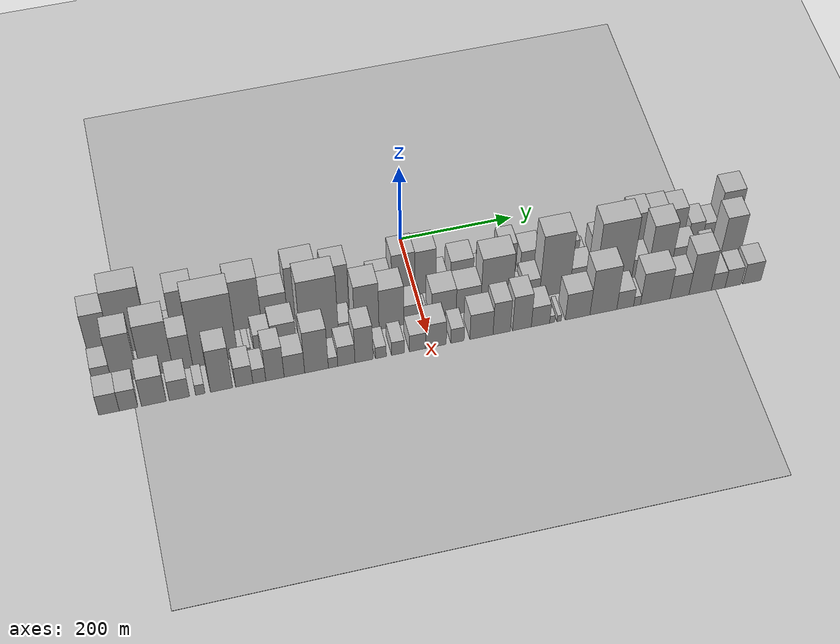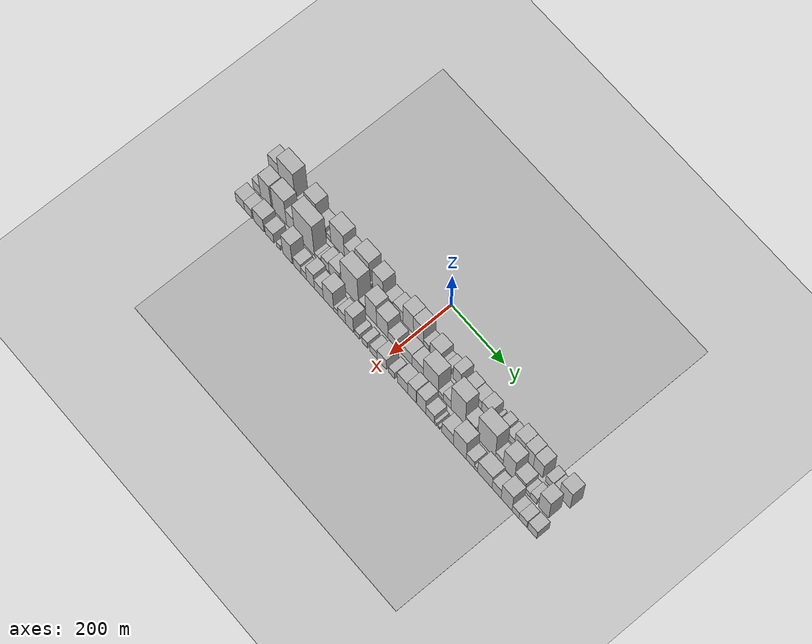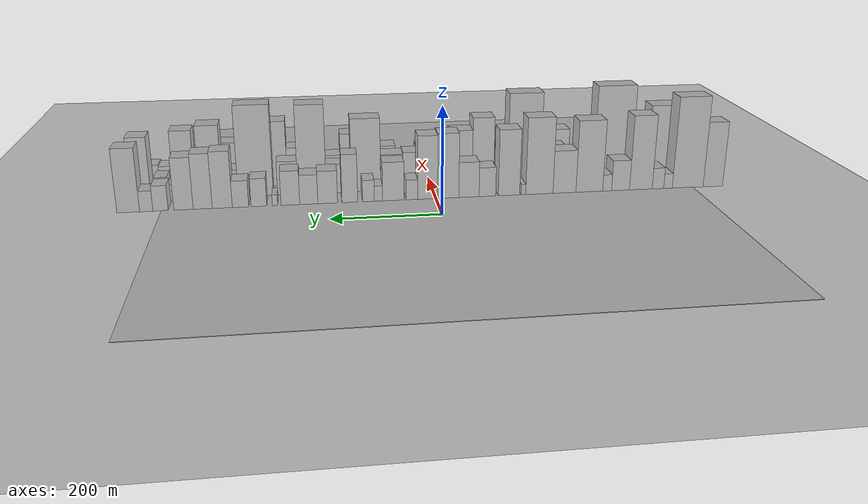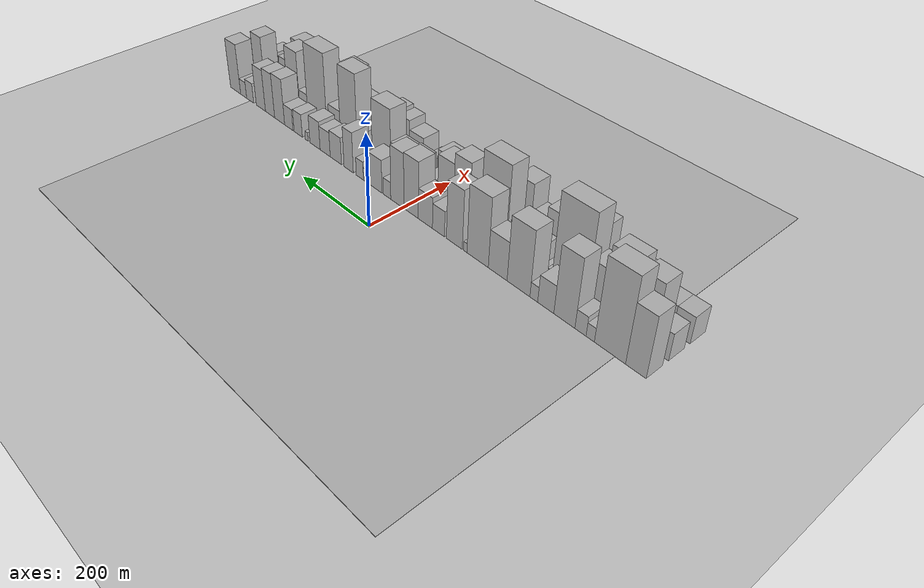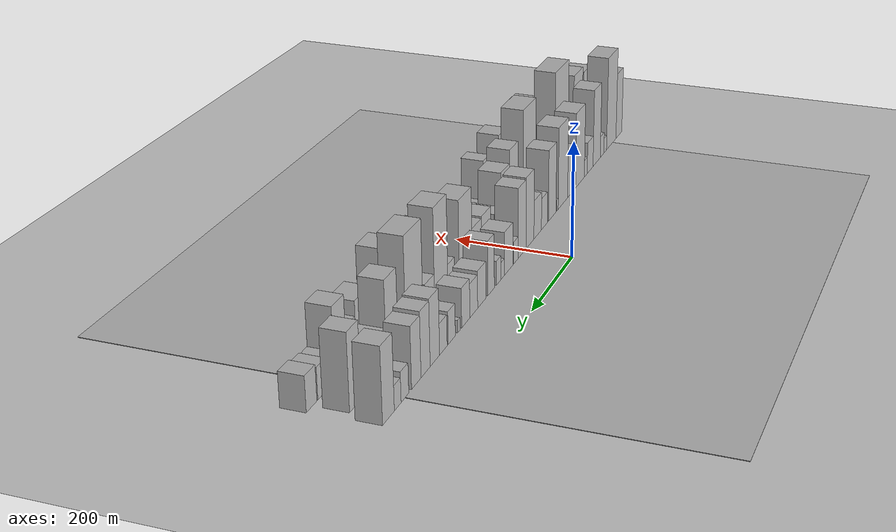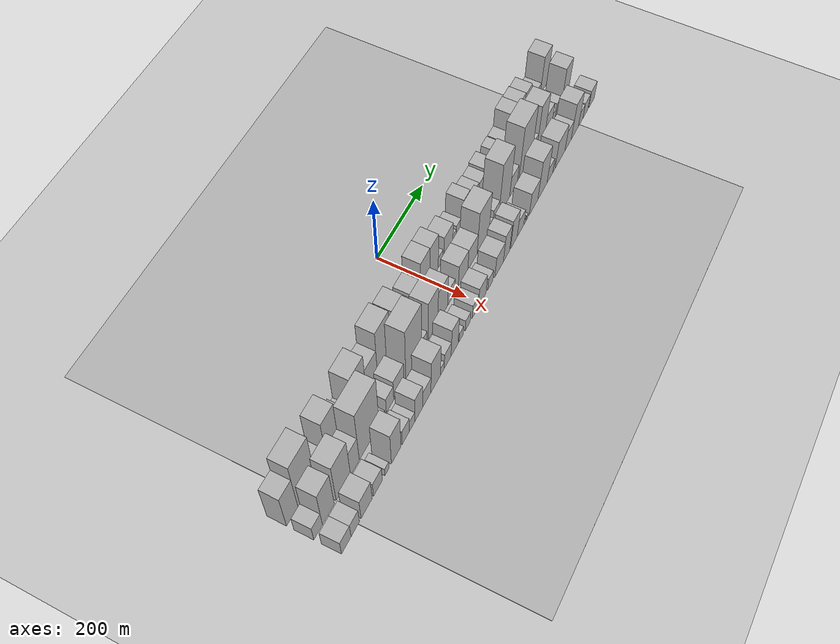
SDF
<?xml version="1.0" encoding="utf-8"?>

<sdf version="1.6">

   <world name="default">

      <gui fullscreen="0">

         <camera name="user_camera">

            <pose>-15 0 4.57585 0 0 0</pose>

            <view_controller>orbit</view_controller>

         </camera>

      </gui>

      <scene>

         <sky>

           <clouds>

             <speed>12</speed>

           </clouds>

         </sky>

         <ambient>0.4 0.4 0.4 1</ambient>

         <background>0.7 0.7 0.7 1</background>

         <shadows>1</shadows>

      </scene>

      <gravity>0 0 -9.8066</gravity>

      <magnetic_field>6e-06 2.3e-05 -4.2e-05</magnetic_field>

      <physics default="0" name="default_physics" type="ode">

         <ode>

            <solver>

               <type>quick</type>

               <iters>10</iters>

               <sor>1.0</sor>

               <use_dynamic_moi_rescaling>0</use_dynamic_moi_rescaling>

            </solver>

            <constraints>

               <cfm>0</cfm>

               <erp>0.2</erp>

               <contact_max_correcting_vel>100</contact_max_correcting_vel>

               <contact_surface_layer>0.001</contact_surface_layer>

            </constraints>

         </ode>

         <max_step_size>0.004</max_step_size>

         <real_time_factor>1</real_time_factor>

         <real_time_update_rate>250</real_time_update_rate>

      </physics>

      <light name="sun" type="directional">

         <cast_shadows>1</cast_shadows>

         <pose>0 0 10 0 0 0</pose>

         <diffuse>0.8 0.8 0.8 1</diffuse>

         <specular>0.2 0.2 0.2 1</specular>

         <attenuation>

            <range>1000</range>

            <constant>0.9</constant>

            <linear>0.01</linear>

            <quadratic>0.001</quadratic>

         </attenuation>

         <direction>-0.5 0.1 -0.9</direction>

      </light>

      <include>

         <name>ground_plane_1</name>

         <uri>model://HANNAS_ground_plane</uri>

         <pose>0 0 0  0 0 0</pose>

      </include>

      <include>

         <name>ground_plane_2</name>

         <uri>model://HANNAS_ground_plane</uri>

         <pose>100 0 0  0 0 0</pose>

      </include>

      <model name="building_1">

         <static>1</static>

         <pose frame="">100.0000 -540.2787 0 0.000000 0.000000 0.000000</pose>

         <link name="link">

            <pose frame="">0 0 64.50 0 0 0</pose>

            <collision name="collision">

               <geometry>

                  <box>

                     <size>40.0000 39.4425 129.0000</size>

                  </box>

               </geometry>

               <max_contacts>10</max_contacts>

               <surface>

                  <contact>

                     <ode/>

                  </contact>

                  <bounce/>

                  <friction>

                     <torsional>

                        <ode/>

                     </torsional>

                     <ode/>

                  </friction>

               </surface>

            </collision>

            <visual name="visual">

               <cast_shadows>0</cast_shadows>

               <geometry>

                  <box>

                     <size>40.0000 39.4425 129.0000</size>

                  </box>

               </geometry>

               <material>

                  <script>

                     <uri>model://HANNAS_wall/materials/scripts</uri>

                     <uri>model://HANNAS_wall/materials/textures</uri>

                     <name>vrc/HANNAS_wall</name>

                  </script>

               </material>

            </visual>

            <self_collide>0</self_collide>

            <enable_wind>0</enable_wind>

            <kinematic>0</kinematic>

         </link>

      </model>

      <model name="building_2">

         <static>1</static>

         <pose frame="">100.0000 -489.5834 0 0.000000 0.000000 0.000000</pose>

         <link name="link">

            <pose frame="">0 0 90.00 0 0 0</pose>

            <collision name="collision">

               <geometry>

                  <box>

                     <size>40.0000 61.9483 180.0000</size>

                  </box>

               </geometry>

               <max_contacts>10</max_contacts>

               <surface>

                  <contact>

                     <ode/>

                  </contact>

                  <bounce/>

                  <friction>

                     <torsional>

                        <ode/>

                     </torsional>

                     <ode/>

                  </friction>

               </surface>

            </collision>

            <visual name="visual">

               <cast_shadows>0</cast_shadows>

               <geometry>

                  <box>

                     <size>40.0000 61.9483 180.0000</size>

                  </box>

               </geometry>

               <material>

                  <script>

                     <uri>model://HANNAS_wall/materials/scripts</uri>

                     <uri>model://HANNAS_wall/materials/textures</uri>

                     <name>vrc/HANNAS_wall</name>

                  </script>

               </material>

            </visual>

            <self_collide>0</self_collide>

            <enable_wind>0</enable_wind>

            <kinematic>0</kinematic>

         </link>

      </model>

      <model name="building_3">

         <static>1</static>

         <pose frame="">100.0000 -450.0688 0 0.000000 0.000000 0.000000</pose>

         <link name="link">

            <pose frame="">0 0 15.00 0 0 0</pose>

            <collision name="collision">

               <geometry>

                  <box>

                     <size>40.0000 17.0808 30.0000</size>

                  </box>

               </geometry>

               <max_contacts>10</max_contacts>

               <surface>

                  <contact>

                     <ode/>

                  </contact>

                  <bounce/>

                  <friction>

                     <torsional>

                        <ode/>

                     </torsional>

                     <ode/>

                  </friction>

               </surface>

            </collision>

            <visual name="visual">

               <cast_shadows>0</cast_shadows>

               <geometry>

                  <box>

                     <size>40.0000 17.0808 30.0000</size>

                  </box>

               </geometry>

               <material>

                  <script>

                     <uri>model://HANNAS_wall/materials/scripts</uri>

                     <uri>model://HANNAS_wall/materials/textures</uri>

                     <name>vrc/HANNAS_wall</name>

                  </script>

               </material>

            </visual>

            <self_collide>0</self_collide>

            <enable_wind>0</enable_wind>

            <kinematic>0</kinematic>

         </link>

      </model>

      <model name="building_4">

         <static>1</static>

         <pose frame="">100.0000 -429.9862 0 0.000000 0.000000 0.000000</pose>

         <link name="link">

            <pose frame="">0 0 21.00 0 0 0</pose>

            <collision name="collision">

               <geometry>

                  <box>

                     <size>40.0000 23.0844 42.0000</size>

                  </box>

               </geometry>

               <max_contacts>10</max_contacts>

               <surface>

                  <contact>

                     <ode/>

                  </contact>

                  <bounce/>

                  <friction>

                     <torsional>

                        <ode/>

                     </torsional>

                     <ode/>

                  </friction>

               </surface>

            </collision>

            <visual name="visual">

               <cast_shadows>0</cast_shadows>

               <geometry>

                  <box>

                     <size>40.0000 23.0844 42.0000</size>

                  </box>

               </geometry>

               <material>

                  <script>

                     <uri>model://HANNAS_wall/materials/scripts</uri>

                     <uri>model://HANNAS_wall/materials/textures</uri>

                     <name>vrc/HANNAS_wall</name>

                  </script>

               </material>

            </visual>

            <self_collide>0</self_collide>

            <enable_wind>0</enable_wind>

            <kinematic>0</kinematic>

         </link>

      </model>

      <model name="building_5">

         <static>1</static>

         <pose frame="">100.0000 -395.9503 0 0.000000 0.000000 0.000000</pose>

         <link name="link">

            <pose frame="">0 0 73.50 0 0 0</pose>

            <collision name="collision">

               <geometry>

                  <box>

                     <size>40.0000 44.9876 147.0000</size>

                  </box>

               </geometry>

               <max_contacts>10</max_contacts>

               <surface>

                  <contact>

                     <ode/>

                  </contact>

                  <bounce/>

                  <friction>

                     <torsional>

                        <ode/>

                     </torsional>

                     <ode/>

                  </friction>

               </surface>

            </collision>

            <visual name="visual">

               <cast_shadows>0</cast_shadows>

               <geometry>

                  <box>

                     <size>40.0000 44.9876 147.0000</size>

                  </box>

               </geometry>

               <material>

                  <script>

                     <uri>model://HANNAS_wall/materials/scripts</uri>

                     <uri>model://HANNAS_wall/materials/textures</uri>

                     <name>vrc/HANNAS_wall</name>

                  </script>

               </material>

            </visual>

            <self_collide>0</self_collide>

            <enable_wind>0</enable_wind>

            <kinematic>0</kinematic>

         </link>

      </model>

      <model name="building_6">

         <static>1</static>

         <pose frame="">100.0000 -355.6805 0 0.000000 0.000000 0.000000</pose>

         <link name="link">

            <pose frame="">0 0 30.00 0 0 0</pose>

            <collision name="collision">

               <geometry>

                  <box>

                     <size>40.0000 35.5519 60.0000</size>

                  </box>

               </geometry>

               <max_contacts>10</max_contacts>

               <surface>

                  <contact>

                     <ode/>

                  </contact>

                  <bounce/>

                  <friction>

                     <torsional>

                        <ode/>

                     </torsional>

                     <ode/>

                  </friction>

               </surface>

            </collision>

            <visual name="visual">

               <cast_shadows>0</cast_shadows>

               <geometry>

                  <box>

                     <size>40.0000 35.5519 60.0000</size>

                  </box>

               </geometry>

               <material>

                  <script>

                     <uri>model://HANNAS_wall/materials/scripts</uri>

                     <uri>model://HANNAS_wall/materials/textures</uri>

                     <name>vrc/HANNAS_wall</name>

                  </script>

               </material>

            </visual>

            <self_collide>0</self_collide>

            <enable_wind>0</enable_wind>

            <kinematic>0</kinematic>

         </link>

      </model>

      <model name="building_7">

         <static>1</static>

         <pose frame="">100.0000 -329.2143 0 0.000000 0.000000 0.000000</pose>

         <link name="link">

            <pose frame="">0 0 16.50 0 0 0</pose>

            <collision name="collision">

               <geometry>

                  <box>

                     <size>40.0000 17.3806 33.0000</size>

                  </box>

               </geometry>

               <max_contacts>10</max_contacts>

               <surface>

                  <contact>

                     <ode/>

                  </contact>

                  <bounce/>

                  <friction>

                     <torsional>

                        <ode/>

                     </torsional>

                     <ode/>

                  </friction>

               </surface>

            </collision>

            <visual name="visual">

               <cast_shadows>0</cast_shadows>

               <geometry>

                  <box>

                     <size>40.0000 17.3806 33.0000</size>

                  </box>

               </geometry>

               <material>

                  <script>

                     <uri>model://HANNAS_wall/materials/scripts</uri>

                     <uri>model://HANNAS_wall/materials/textures</uri>

                     <name>vrc/HANNAS_wall</name>

                  </script>

               </material>

            </visual>

            <self_collide>0</self_collide>

            <enable_wind>0</enable_wind>

            <kinematic>0</kinematic>

         </link>

      </model>

      <model name="building_8">

         <static>1</static>

         <pose frame="">100.0000 -294.2774 0 0.000000 0.000000 0.000000</pose>

         <link name="link">

            <pose frame="">0 0 70.50 0 0 0</pose>

            <collision name="collision">

               <geometry>

                  <box>

                     <size>40.0000 52.4931 141.0000</size>

                  </box>

               </geometry>

               <max_contacts>10</max_contacts>

               <surface>

                  <contact>

                     <ode/>

                  </contact>

                  <bounce/>

                  <friction>

                     <torsional>

                        <ode/>

                     </torsional>

                     <ode/>

                  </friction>

               </surface>

            </collision>

            <visual name="visual">

               <cast_shadows>0</cast_shadows>

               <geometry>

                  <box>

                     <size>40.0000 52.4931 141.0000</size>

                  </box>

               </geometry>

               <material>

                  <script>

                     <uri>model://HANNAS_wall/materials/scripts</uri>

                     <uri>model://HANNAS_wall/materials/textures</uri>

                     <name>vrc/HANNAS_wall</name>

                  </script>

               </material>

            </visual>

            <self_collide>0</self_collide>

            <enable_wind>0</enable_wind>

            <kinematic>0</kinematic>

         </link>

      </model>

      <model name="building_9">

         <static>1</static>

         <pose frame="">100.0000 -245.6780 0 0.000000 0.000000 0.000000</pose>

         <link name="link">

            <pose frame="">0 0 42.00 0 0 0</pose>

            <collision name="collision">

               <geometry>

                  <box>

                     <size>40.0000 44.7058 84.0000</size>

                  </box>

               </geometry>

               <max_contacts>10</max_contacts>

               <surface>

                  <contact>

                     <ode/>

                  </contact>

                  <bounce/>

                  <friction>

                     <torsional>

                        <ode/>

                     </torsional>

                     <ode/>

                  </friction>

               </surface>

            </collision>

            <visual name="visual">

               <cast_shadows>0</cast_shadows>

               <geometry>

                  <box>

                     <size>40.0000 44.7058 84.0000</size>

                  </box>

               </geometry>

               <material>

                  <script>

                     <uri>model://HANNAS_wall/materials/scripts</uri>

                     <uri>model://HANNAS_wall/materials/textures</uri>

                     <name>vrc/HANNAS_wall</name>

                  </script>

               </material>

            </visual>

            <self_collide>0</self_collide>

            <enable_wind>0</enable_wind>

            <kinematic>0</kinematic>

         </link>

      </model>

      <model name="building_10">

         <static>1</static>

         <pose frame="">100.0000 -196.9684 0 0.000000 0.000000 0.000000</pose>

         <link name="link">

            <pose frame="">0 0 75.00 0 0 0</pose>

            <collision name="collision">

               <geometry>

                  <box>

                     <size>40.0000 52.7134 150.0000</size>

                  </box>

               </geometry>

               <max_contacts>10</max_contacts>

               <surface>

                  <contact>

                     <ode/>

                  </contact>

                  <bounce/>

                  <friction>

                     <torsional>

                        <ode/>

                     </torsional>

                     <ode/>

                  </friction>

               </surface>

            </collision>

            <visual name="visual">

               <cast_shadows>0</cast_shadows>

               <geometry>

                  <box>

                     <size>40.0000 52.7134 150.0000</size>

                  </box>

               </geometry>

               <material>

                  <script>

                     <uri>model://HANNAS_wall/materials/scripts</uri>

                     <uri>model://HANNAS_wall/materials/textures</uri>

                     <name>vrc/HANNAS_wall</name>

                  </script>

               </material>

            </visual>

            <self_collide>0</self_collide>

            <enable_wind>0</enable_wind>

            <kinematic>0</kinematic>

         </link>

      </model>

      <model name="building_11">

         <static>1</static>

         <pose frame="">100.0000 -166.2816 0 0.000000 0.000000 0.000000</pose>

         <link name="link">

            <pose frame="">0 0 10.50 0 0 0</pose>

            <collision name="collision">

               <geometry>

                  <box>

                     <size>40.0000 8.6601 21.0000</size>

                  </box>

               </geometry>

               <max_contacts>10</max_contacts>

               <surface>

                  <contact>

                     <ode/>

                  </contact>

                  <bounce/>

                  <friction>

                     <torsional>

                        <ode/>

                     </torsional>

                     <ode/>

                  </friction>

               </surface>

            </collision>

            <visual name="visual">

               <cast_shadows>0</cast_shadows>

               <geometry>

                  <box>

                     <size>40.0000 8.6601 21.0000</size>

                  </box>

               </geometry>

               <material>

                  <script>

                     <uri>model://HANNAS_wall/materials/scripts</uri>

                     <uri>model://HANNAS_wall/materials/textures</uri>

                     <name>vrc/HANNAS_wall</name>

                  </script>

               </material>

            </visual>

            <self_collide>0</self_collide>

            <enable_wind>0</enable_wind>

            <kinematic>0</kinematic>

         </link>

      </model>

      <model name="building_12">

         <static>1</static>

         <pose frame="">100.0000 -138.4659 0 0.000000 0.000000 0.000000</pose>

         <link name="link">

            <pose frame="">0 0 64.50 0 0 0</pose>

            <collision name="collision">

               <geometry>

                  <box>

                     <size>40.0000 40.9712 129.0000</size>

                  </box>

               </geometry>

               <max_contacts>10</max_contacts>

               <surface>

                  <contact>

                     <ode/>

                  </contact>

                  <bounce/>

                  <friction>

                     <torsional>

                        <ode/>

                     </torsional>

                     <ode/>

                  </friction>

               </surface>

            </collision>

            <visual name="visual">

               <cast_shadows>0</cast_shadows>

               <geometry>

                  <box>

                     <size>40.0000 40.9712 129.0000</size>

                  </box>

               </geometry>

               <material>

                  <script>

                     <uri>model://HANNAS_wall/materials/scripts</uri>

                     <uri>model://HANNAS_wall/materials/textures</uri>

                     <name>vrc/HANNAS_wall</name>

                  </script>

               </material>

            </visual>

            <self_collide>0</self_collide>

            <enable_wind>0</enable_wind>

            <kinematic>0</kinematic>

         </link>

      </model>

      <model name="building_13">

         <static>1</static>

         <pose frame="">100.0000 -97.1301 0 0.000000 0.000000 0.000000</pose>

         <link name="link">

            <pose frame="">0 0 28.50 0 0 0</pose>

            <collision name="collision">

               <geometry>

                  <box>

                     <size>40.0000 31.7005 57.0000</size>

                  </box>

               </geometry>

               <max_contacts>10</max_contacts>

               <surface>

                  <contact>

                     <ode/>

                  </contact>

                  <bounce/>

                  <friction>

                     <torsional>

                        <ode/>

                     </torsional>

                     <ode/>

                  </friction>

               </surface>

            </collision>

            <visual name="visual">

               <cast_shadows>0</cast_shadows>

               <geometry>

                  <box>

                     <size>40.0000 31.7005 57.0000</size>

                  </box>

               </geometry>

               <material>

                  <script>

                     <uri>model://HANNAS_wall/materials/scripts</uri>

                     <uri>model://HANNAS_wall/materials/textures</uri>

                     <name>vrc/HANNAS_wall</name>

                  </script>

               </material>

            </visual>

            <self_collide>0</self_collide>

            <enable_wind>0</enable_wind>

            <kinematic>0</kinematic>

         </link>

      </model>

      <model name="building_14">

         <static>1</static>

         <pose frame="">100.0000 -62.0921 0 0.000000 0.000000 0.000000</pose>

         <link name="link">

            <pose frame="">0 0 34.50 0 0 0</pose>

            <collision name="collision">

               <geometry>

                  <box>

                     <size>40.0000 38.3755 69.0000</size>

                  </box>

               </geometry>

               <max_contacts>10</max_contacts>

               <surface>

                  <contact>

                     <ode/>

                  </contact>

                  <bounce/>

                  <friction>

                     <torsional>

                        <ode/>

                     </torsional>

                     <ode/>

                  </friction>

               </surface>

            </collision>

            <visual name="visual">

               <cast_shadows>0</cast_shadows>

               <geometry>

                  <box>

                     <size>40.0000 38.3755 69.0000</size>

                  </box>

               </geometry>

               <material>

                  <script>

                     <uri>model://HANNAS_wall/materials/scripts</uri>

                     <uri>model://HANNAS_wall/materials/textures</uri>

                     <name>vrc/HANNAS_wall</name>

                  </script>

               </material>

            </visual>

            <self_collide>0</self_collide>

            <enable_wind>0</enable_wind>

            <kinematic>0</kinematic>

         </link>

      </model>

      <model name="building_15">

         <static>1</static>

         <pose frame="">100.0000 -22.9178 0 0.000000 0.000000 0.000000</pose>

         <link name="link">

            <pose frame="">0 0 63.00 0 0 0</pose>

            <collision name="collision">

               <geometry>

                  <box>

                     <size>40.0000 39.9730 126.0000</size>

                  </box>

               </geometry>

               <max_contacts>10</max_contacts>

               <surface>

                  <contact>

                     <ode/>

                  </contact>

                  <bounce/>

                  <friction>

                     <torsional>

                        <ode/>

                     </torsional>

                     <ode/>

                  </friction>

               </surface>

            </collision>

            <visual name="visual">

               <cast_shadows>0</cast_shadows>

               <geometry>

                  <box>

                     <size>40.0000 39.9730 126.0000</size>

                  </box>

               </geometry>

               <material>

                  <script>

                     <uri>model://HANNAS_wall/materials/scripts</uri>

                     <uri>model://HANNAS_wall/materials/textures</uri>

                     <name>vrc/HANNAS_wall</name>

                  </script>

               </material>

            </visual>

            <self_collide>0</self_collide>

            <enable_wind>0</enable_wind>

            <kinematic>0</kinematic>

         </link>

      </model>

      <model name="building_16">

         <static>1</static>

         <pose frame="">100.0000 15.6804 0 0.000000 0.000000 0.000000</pose>

         <link name="link">

            <pose frame="">0 0 61.50 0 0 0</pose>

            <collision name="collision">

               <geometry>

                  <box>

                     <size>40.0000 37.2234 123.0000</size>

                  </box>

               </geometry>

               <max_contacts>10</max_contacts>

               <surface>

                  <contact>

                     <ode/>

                  </contact>

                  <bounce/>

                  <friction>

                     <torsional>

                        <ode/>

                     </torsional>

                     <ode/>

                  </friction>

               </surface>

            </collision>

            <visual name="visual">

               <cast_shadows>0</cast_shadows>

               <geometry>

                  <box>

                     <size>40.0000 37.2234 123.0000</size>

                  </box>

               </geometry>

               <material>

                  <script>

                     <uri>model://HANNAS_wall/materials/scripts</uri>

                     <uri>model://HANNAS_wall/materials/textures</uri>

                     <name>vrc/HANNAS_wall</name>

                  </script>

               </material>

            </visual>

            <self_collide>0</self_collide>

            <enable_wind>0</enable_wind>

            <kinematic>0</kinematic>

         </link>

      </model>

      <model name="building_17">

         <static>1</static>

         <pose frame="">100.0000 45.0935 0 0.000000 0.000000 0.000000</pose>

         <link name="link">

            <pose frame="">0 0 19.50 0 0 0</pose>

            <collision name="collision">

               <geometry>

                  <box>

                     <size>40.0000 21.6028 39.0000</size>

                  </box>

               </geometry>

               <max_contacts>10</max_contacts>

               <surface>

                  <contact>

                     <ode/>

                  </contact>

                  <bounce/>

                  <friction>

                     <torsional>

                        <ode/>

                     </torsional>

                     <ode/>

                  </friction>

               </surface>

            </collision>

            <visual name="visual">

               <cast_shadows>0</cast_shadows>

               <geometry>

                  <box>

                     <size>40.0000 21.6028 39.0000</size>

                  </box>

               </geometry>

               <material>

                  <script>

                     <uri>model://HANNAS_wall/materials/scripts</uri>

                     <uri>model://HANNAS_wall/materials/textures</uri>

                     <name>vrc/HANNAS_wall</name>

                  </script>

               </material>

            </visual>

            <self_collide>0</self_collide>

            <enable_wind>0</enable_wind>

            <kinematic>0</kinematic>

         </link>

      </model>

      <model name="building_18">

         <static>1</static>

         <pose frame="">100.0000 79.9457 0 0.000000 0.000000 0.000000</pose>

         <link name="link">

            <pose frame="">0 0 37.50 0 0 0</pose>

            <collision name="collision">

               <geometry>

                  <box>

                     <size>40.0000 40.1015 75.0000</size>

                  </box>

               </geometry>

               <max_contacts>10</max_contacts>

               <surface>

                  <contact>

                     <ode/>

                  </contact>

                  <bounce/>

                  <friction>

                     <torsional>

                        <ode/>

                     </torsional>

                     <ode/>

                  </friction>

               </surface>

            </collision>

            <visual name="visual">

               <cast_shadows>0</cast_shadows>

               <geometry>

                  <box>

                     <size>40.0000 40.1015 75.0000</size>

                  </box>

               </geometry>

               <material>

                  <script>

                     <uri>model://HANNAS_wall/materials/scripts</uri>

                     <uri>model://HANNAS_wall/materials/textures</uri>

                     <name>vrc/HANNAS_wall</name>

                  </script>

               </material>

            </visual>

            <self_collide>0</self_collide>

            <enable_wind>0</enable_wind>

            <kinematic>0</kinematic>

         </link>

      </model>

      <model name="building_19">

         <static>1</static>

         <pose frame="">100.0000 107.7199 0 0.000000 0.000000 0.000000</pose>

         <link name="link">

            <pose frame="">0 0 15.00 0 0 0</pose>

            <collision name="collision">

               <geometry>

                  <box>

                     <size>40.0000 15.4468 30.0000</size>

                  </box>

               </geometry>

               <max_contacts>10</max_contacts>

               <surface>

                  <contact>

                     <ode/>

                  </contact>

                  <bounce/>

                  <friction>

                     <torsional>

                        <ode/>

                     </torsional>

                     <ode/>

                  </friction>

               </surface>

            </collision>

            <visual name="visual">

               <cast_shadows>0</cast_shadows>

               <geometry>

                  <box>

                     <size>40.0000 15.4468 30.0000</size>

                  </box>

               </geometry>

               <material>

                  <script>

                     <uri>model://HANNAS_wall/materials/scripts</uri>

                     <uri>model://HANNAS_wall/materials/textures</uri>

                     <name>vrc/HANNAS_wall</name>

                  </script>

               </material>

            </visual>

            <self_collide>0</self_collide>

            <enable_wind>0</enable_wind>

            <kinematic>0</kinematic>

         </link>

      </model>

      <model name="building_20">

         <static>1</static>

         <pose frame="">100.0000 126.3243 0 0.000000 0.000000 0.000000</pose>

         <link name="link">

            <pose frame="">0 0 21.00 0 0 0</pose>

            <collision name="collision">

               <geometry>

                  <box>

                     <size>40.0000 21.7621 42.0000</size>

                  </box>

               </geometry>

               <max_contacts>10</max_contacts>

               <surface>

                  <contact>

                     <ode/>

                  </contact>

                  <bounce/>

                  <friction>

                     <torsional>

                        <ode/>

                     </torsional>

                     <ode/>

                  </friction>

               </surface>

            </collision>

            <visual name="visual">

               <cast_shadows>0</cast_shadows>

               <geometry>

                  <box>

                     <size>40.0000 21.7621 42.0000</size>

                  </box>

               </geometry>

               <material>

                  <script>

                     <uri>model://HANNAS_wall/materials/scripts</uri>

                     <uri>model://HANNAS_wall/materials/textures</uri>

                     <name>vrc/HANNAS_wall</name>

                  </script>

               </material>

            </visual>

            <self_collide>0</self_collide>

            <enable_wind>0</enable_wind>

            <kinematic>0</kinematic>

         </link>

      </model>

      <model name="building_21">

         <static>1</static>

         <pose frame="">100.0000 160.7265 0 0.000000 0.000000 0.000000</pose>

         <link name="link">

            <pose frame="">0 0 46.50 0 0 0</pose>

            <collision name="collision">

               <geometry>

                  <box>

                     <size>40.0000 29.0423 93.0000</size>

                  </box>

               </geometry>

               <max_contacts>10</max_contacts>

               <surface>

                  <contact>

                     <ode/>

                  </contact>

                  <bounce/>

                  <friction>

                     <torsional>

                        <ode/>

                     </torsional>

                     <ode/>

                  </friction>

               </surface>

            </collision>

            <visual name="visual">

               <cast_shadows>0</cast_shadows>

               <geometry>

                  <box>

                     <size>40.0000 29.0423 93.0000</size>

                  </box>

               </geometry>

               <material>

                  <script>

                     <uri>model://HANNAS_wall/materials/scripts</uri>

                     <uri>model://HANNAS_wall/materials/textures</uri>

                     <name>vrc/HANNAS_wall</name>

                  </script>

               </material>

            </visual>

            <self_collide>0</self_collide>

            <enable_wind>0</enable_wind>

            <kinematic>0</kinematic>

         </link>

      </model>

      <model name="building_22">

         <static>1</static>

         <pose frame="">100.0000 201.3074 0 0.000000 0.000000 0.000000</pose>

         <link name="link">

            <pose frame="">0 0 31.50 0 0 0</pose>

            <collision name="collision">

               <geometry>

                  <box>

                     <size>40.0000 36.1193 63.0000</size>

                  </box>

               </geometry>

               <max_contacts>10</max_contacts>

               <surface>

                  <contact>

                     <ode/>

                  </contact>

                  <bounce/>

                  <friction>

                     <torsional>

                        <ode/>

                     </torsional>

                     <ode/>

                  </friction>

               </surface>

            </collision>

            <visual name="visual">

               <cast_shadows>0</cast_shadows>

               <geometry>

                  <box>

                     <size>40.0000 36.1193 63.0000</size>

                  </box>

               </geometry>

               <material>

                  <script>

                     <uri>model://HANNAS_wall/materials/scripts</uri>

                     <uri>model://HANNAS_wall/materials/textures</uri>

                     <name>vrc/HANNAS_wall</name>

                  </script>

               </material>

            </visual>

            <self_collide>0</self_collide>

            <enable_wind>0</enable_wind>

            <kinematic>0</kinematic>

         </link>

      </model>

      <model name="building_23">

         <static>1</static>

         <pose frame="">100.0000 235.8626 0 0.000000 0.000000 0.000000</pose>

         <link name="link">

            <pose frame="">0 0 28.50 0 0 0</pose>

            <collision name="collision">

               <geometry>

                  <box>

                     <size>40.0000 32.9910 57.0000</size>

                  </box>

               </geometry>

               <max_contacts>10</max_contacts>

               <surface>

                  <contact>

                     <ode/>

                  </contact>

                  <bounce/>

                  <friction>

                     <torsional>

                        <ode/>

                     </torsional>

                     <ode/>

                  </friction>

               </surface>

            </collision>

            <visual name="visual">

               <cast_shadows>0</cast_shadows>

               <geometry>

                  <box>

                     <size>40.0000 32.9910 57.0000</size>

                  </box>

               </geometry>

               <material>

                  <script>

                     <uri>model://HANNAS_wall/materials/scripts</uri>

                     <uri>model://HANNAS_wall/materials/textures</uri>

                     <name>vrc/HANNAS_wall</name>

                  </script>

               </material>

            </visual>

            <self_collide>0</self_collide>

            <enable_wind>0</enable_wind>

            <kinematic>0</kinematic>

         </link>

      </model>

      <model name="building_24">

         <static>1</static>

         <pose frame="">100.0000 269.3877 0 0.000000 0.000000 0.000000</pose>

         <link name="link">

            <pose frame="">0 0 33.00 0 0 0</pose>

            <collision name="collision">

               <geometry>

                  <box>

                     <size>40.0000 34.0592 66.0000</size>

                  </box>

               </geometry>

               <max_contacts>10</max_contacts>

               <surface>

                  <contact>

                     <ode/>

                  </contact>

                  <bounce/>

                  <friction>

                     <torsional>

                        <ode/>

                     </torsional>

                     <ode/>

                  </friction>

               </surface>

            </collision>

            <visual name="visual">

               <cast_shadows>0</cast_shadows>

               <geometry>

                  <box>

                     <size>40.0000 34.0592 66.0000</size>

                  </box>

               </geometry>

               <material>

                  <script>

                     <uri>model://HANNAS_wall/materials/scripts</uri>

                     <uri>model://HANNAS_wall/materials/textures</uri>

                     <name>vrc/HANNAS_wall</name>

                  </script>

               </material>

            </visual>

            <self_collide>0</self_collide>

            <enable_wind>0</enable_wind>

            <kinematic>0</kinematic>

         </link>

      </model>

      <model name="building_25">

         <static>1</static>

         <pose frame="">100.0000 297.2625 0 0.000000 0.000000 0.000000</pose>

         <link name="link">

            <pose frame="">0 0 10.50 0 0 0</pose>

            <collision name="collision">

               <geometry>

                  <box>

                     <size>40.0000 9.6904 21.0000</size>

                  </box>

               </geometry>

               <max_contacts>10</max_contacts>

               <surface>

                  <contact>

                     <ode/>

                  </contact>

                  <bounce/>

                  <friction>

                     <torsional>

                        <ode/>

                     </torsional>

                     <ode/>

                  </friction>

               </surface>

            </collision>

            <visual name="visual">

               <cast_shadows>0</cast_shadows>

               <geometry>

                  <box>

                     <size>40.0000 9.6904 21.0000</size>

                  </box>

               </geometry>

               <material>

                  <script>

                     <uri>model://HANNAS_wall/materials/scripts</uri>

                     <uri>model://HANNAS_wall/materials/textures</uri>

                     <name>vrc/HANNAS_wall</name>

                  </script>

               </material>

            </visual>

            <self_collide>0</self_collide>

            <enable_wind>0</enable_wind>

            <kinematic>0</kinematic>

         </link>

      </model>

      <model name="building_26">

         <static>1</static>

         <pose frame="">100.0000 326.2790 0 0.000000 0.000000 0.000000</pose>

         <link name="link">

            <pose frame="">0 0 27.00 0 0 0</pose>

            <collision name="collision">

               <geometry>

                  <box>

                     <size>40.0000 28.3426 54.0000</size>

                  </box>

               </geometry>

               <max_contacts>10</max_contacts>

               <surface>

                  <contact>

                     <ode/>

                  </contact>

                  <bounce/>

                  <friction>

                     <torsional>

                        <ode/>

                     </torsional>

                     <ode/>

                  </friction>

               </surface>

            </collision>

            <visual name="visual">

               <cast_shadows>0</cast_shadows>

               <geometry>

                  <box>

                     <size>40.0000 28.3426 54.0000</size>

                  </box>

               </geometry>

               <material>

                  <script>

                     <uri>model://HANNAS_wall/materials/scripts</uri>

                     <uri>model://HANNAS_wall/materials/textures</uri>

                     <name>vrc/HANNAS_wall</name>

                  </script>

               </material>

            </visual>

            <self_collide>0</self_collide>

            <enable_wind>0</enable_wind>

            <kinematic>0</kinematic>

         </link>

      </model>

      <model name="building_27">

         <static>1</static>

         <pose frame="">100.0000 359.1758 0 0.000000 0.000000 0.000000</pose>

         <link name="link">

            <pose frame="">0 0 25.50 0 0 0</pose>

            <collision name="collision">

               <geometry>

                  <box>

                     <size>40.0000 29.4510 51.0000</size>

                  </box>

               </geometry>

               <max_contacts>10</max_contacts>

               <surface>

                  <contact>

                     <ode/>

                  </contact>

                  <bounce/>

                  <friction>

                     <torsional>

                        <ode/>

                     </torsional>

                     <ode/>

                  </friction>

               </surface>

            </collision>

            <visual name="visual">

               <cast_shadows>0</cast_shadows>

               <geometry>

                  <box>

                     <size>40.0000 29.4510 51.0000</size>

                  </box>

               </geometry>

               <material>

                  <script>

                     <uri>model://HANNAS_wall/materials/scripts</uri>

                     <uri>model://HANNAS_wall/materials/textures</uri>

                     <name>vrc/HANNAS_wall</name>

                  </script>

               </material>

            </visual>

            <self_collide>0</self_collide>

            <enable_wind>0</enable_wind>

            <kinematic>0</kinematic>

         </link>

      </model>

      <model name="building_28">

         <static>1</static>

         <pose frame="">100.0000 391.7978 0 0.000000 0.000000 0.000000</pose>

         <link name="link">

            <pose frame="">0 0 54.00 0 0 0</pose>

            <collision name="collision">

               <geometry>

                  <box>

                     <size>40.0000 35.7929 108.0000</size>

                  </box>

               </geometry>

               <max_contacts>10</max_contacts>

               <surface>

                  <contact>

                     <ode/>

                  </contact>

                  <bounce/>

                  <friction>

                     <torsional>

                        <ode/>

                     </torsional>

                     <ode/>

                  </friction>

               </surface>

            </collision>

            <visual name="visual">

               <cast_shadows>0</cast_shadows>

               <geometry>

                  <box>

                     <size>40.0000 35.7929 108.0000</size>

                  </box>

               </geometry>

               <material>

                  <script>

                     <uri>model://HANNAS_wall/materials/scripts</uri>

                     <uri>model://HANNAS_wall/materials/textures</uri>

                     <name>vrc/HANNAS_wall</name>

                  </script>

               </material>

            </visual>

            <self_collide>0</self_collide>

            <enable_wind>0</enable_wind>

            <kinematic>0</kinematic>

         </link>

      </model>

      <model name="building_29">

         <static>1</static>

         <pose frame="">100.0000 426.5890 0 0.000000 0.000000 0.000000</pose>

         <link name="link">

            <pose frame="">0 0 52.50 0 0 0</pose>

            <collision name="collision">

               <geometry>

                  <box>

                     <size>40.0000 33.7896 105.0000</size>

                  </box>

               </geometry>

               <max_contacts>10</max_contacts>

               <surface>

                  <contact>

                     <ode/>

                  </contact>

                  <bounce/>

                  <friction>

                     <torsional>

                        <ode/>

                     </torsional>

                     <ode/>

                  </friction>

               </surface>

            </collision>

            <visual name="visual">

               <cast_shadows>0</cast_shadows>

               <geometry>

                  <box>

                     <size>40.0000 33.7896 105.0000</size>

                  </box>

               </geometry>

               <material>

                  <script>

                     <uri>model://HANNAS_wall/materials/scripts</uri>

                     <uri>model://HANNAS_wall/materials/textures</uri>

                     <name>vrc/HANNAS_wall</name>

                  </script>

               </material>

            </visual>

            <self_collide>0</self_collide>

            <enable_wind>0</enable_wind>

            <kinematic>0</kinematic>

         </link>

      </model>

      <model name="building_30">

         <static>1</static>

         <pose frame="">100.0000 460.5955 0 0.000000 0.000000 0.000000</pose>

         <link name="link">

            <pose frame="">0 0 49.50 0 0 0</pose>

            <collision name="collision">

               <geometry>

                  <box>

                     <size>40.0000 34.2234 99.0000</size>

                  </box>

               </geometry>

               <max_contacts>10</max_contacts>

               <surface>

                  <contact>

                     <ode/>

                  </contact>

                  <bounce/>

                  <friction>

                     <torsional>

                        <ode/>

                     </torsional>

                     <ode/>

                  </friction>

               </surface>

            </collision>

            <visual name="visual">

               <cast_shadows>0</cast_shadows>

               <geometry>

                  <box>

                     <size>40.0000 34.2234 99.0000</size>

                  </box>

               </geometry>

               <material>

                  <script>

                     <uri>model://HANNAS_wall/materials/scripts</uri>

                     <uri>model://HANNAS_wall/materials/textures</uri>

                     <name>vrc/HANNAS_wall</name>

                  </script>

               </material>

            </visual>

            <self_collide>0</self_collide>

            <enable_wind>0</enable_wind>

            <kinematic>0</kinematic>

         </link>

      </model>

      <model name="building_31">

         <static>1</static>

         <pose frame="">100.0000 501.1284 0 0.000000 0.000000 0.000000</pose>

         <link name="link">

            <pose frame="">0 0 24.00 0 0 0</pose>

            <collision name="collision">

               <geometry>

                  <box>

                     <size>40.0000 26.8424 48.0000</size>

                  </box>

               </geometry>

               <max_contacts>10</max_contacts>

               <surface>

                  <contact>

                     <ode/>

                  </contact>

                  <bounce/>

                  <friction>

                     <torsional>

                        <ode/>

                     </torsional>

                     <ode/>

                  </friction>

               </surface>

            </collision>

            <visual name="visual">

               <cast_shadows>0</cast_shadows>

               <geometry>

                  <box>

                     <size>40.0000 26.8424 48.0000</size>

                  </box>

               </geometry>

               <material>

                  <script>

                     <uri>model://HANNAS_wall/materials/scripts</uri>

                     <uri>model://HANNAS_wall/materials/textures</uri>

                     <name>vrc/HANNAS_wall</name>

                  </script>

               </material>

            </visual>

            <self_collide>0</self_collide>

            <enable_wind>0</enable_wind>

            <kinematic>0</kinematic>

         </link>

      </model>

      <model name="building_32">

         <static>1</static>

         <pose frame="">100.0000 526.1630 0 0.000000 0.000000 0.000000</pose>

         <link name="link">

            <pose frame="">0 0 19.50 0 0 0</pose>

            <collision name="collision">

               <geometry>

                  <box>

                     <size>40.0000 23.2268 39.0000</size>

                  </box>

               </geometry>

               <max_contacts>10</max_contacts>

               <surface>

                  <contact>

                     <ode/>

                  </contact>

                  <bounce/>

                  <friction>

                     <torsional>

                        <ode/>

                     </torsional>

                     <ode/>

                  </friction>

               </surface>

            </collision>

            <visual name="visual">

               <cast_shadows>0</cast_shadows>

               <geometry>

                  <box>

                     <size>40.0000 23.2268 39.0000</size>

                  </box>

               </geometry>

               <material>

                  <script>

                     <uri>model://HANNAS_wall/materials/scripts</uri>

                     <uri>model://HANNAS_wall/materials/textures</uri>

                     <name>vrc/HANNAS_wall</name>

                  </script>

               </material>

            </visual>

            <self_collide>0</self_collide>

            <enable_wind>0</enable_wind>

            <kinematic>0</kinematic>

         </link>

      </model>

      <model name="building_33">

         <static>1</static>

         <pose frame="">100.0000 557.6395 0 0.000000 0.000000 0.000000</pose>

         <link name="link">

            <pose frame="">0 0 60.00 0 0 0</pose>

            <collision name="collision">

               <geometry>

                  <box>

                     <size>40.0000 39.7261 120.0000</size>

                  </box>

               </geometry>

               <max_contacts>10</max_contacts>

               <surface>

                  <contact>

                     <ode/>

                  </contact>

                  <bounce/>

                  <friction>

                     <torsional>

                        <ode/>

                     </torsional>

                     <ode/>

                  </friction>

               </surface>

            </collision>

            <visual name="visual">

               <cast_shadows>0</cast_shadows>

               <geometry>

                  <box>

                     <size>40.0000 39.7261 120.0000</size>

                  </box>

               </geometry>

               <material>

                  <script>

                     <uri>model://HANNAS_wall/materials/scripts</uri>

                     <uri>model://HANNAS_wall/materials/textures</uri>

                     <name>vrc/HANNAS_wall</name>

                  </script>

               </material>

            </visual>

            <self_collide>0</self_collide>

            <enable_wind>0</enable_wind>

            <kinematic>0</kinematic>

         </link>

      </model>

      <model name="building_34">

         <static>1</static>

         <pose frame="">155.0000 -544.8172 0 0.000000 0.000000 0.000000</pose>

         <link name="link">

            <pose frame="">0 0 28.50 0 0 0</pose>

            <collision name="collision">

               <geometry>

                  <box>

                     <size>40.0000 30.3655 57.0000</size>

                  </box>

               </geometry>

               <max_contacts>10</max_contacts>

               <surface>

                  <contact>

                     <ode/>

                  </contact>

                  <bounce/>

                  <friction>

                     <torsional>

                        <ode/>

                     </torsional>

                     <ode/>

                  </friction>

               </surface>

            </collision>

            <visual name="visual">

               <cast_shadows>0</cast_shadows>

               <geometry>

                  <box>

                     <size>40.0000 30.3655 57.0000</size>

                  </box>

               </geometry>

               <material>

                  <script>

                     <uri>model://HANNAS_wall/materials/scripts</uri>

                     <uri>model://HANNAS_wall/materials/textures</uri>

                     <name>vrc/HANNAS_wall</name>

                  </script>

               </material>

            </visual>

            <self_collide>0</self_collide>

            <enable_wind>0</enable_wind>

            <kinematic>0</kinematic>

         </link>

      </model>

      <model name="building_35">

         <static>1</static>

         <pose frame="">155.0000 -508.4048 0 0.000000 0.000000 0.000000</pose>

         <link name="link">

            <pose frame="">0 0 69.00 0 0 0</pose>

            <collision name="collision">

               <geometry>

                  <box>

                     <size>40.0000 42.4594 138.0000</size>

                  </box>

               </geometry>

               <max_contacts>10</max_contacts>

               <surface>

                  <contact>

                     <ode/>

                  </contact>

                  <bounce/>

                  <friction>

                     <torsional>

                        <ode/>

                     </torsional>

                     <ode/>

                  </friction>

               </surface>

            </collision>

            <visual name="visual">

               <cast_shadows>0</cast_shadows>

               <geometry>

                  <box>

                     <size>40.0000 42.4594 138.0000</size>

                  </box>

               </geometry>

               <material>

                  <script>

                     <uri>model://HANNAS_wall/materials/scripts</uri>

                     <uri>model://HANNAS_wall/materials/textures</uri>

                     <name>vrc/HANNAS_wall</name>

                  </script>

               </material>

            </visual>

            <self_collide>0</self_collide>

            <enable_wind>0</enable_wind>

            <kinematic>0</kinematic>

         </link>

      </model>

      <model name="building_36">

         <static>1</static>

         <pose frame="">155.0000 -453.7786 0 0.000000 0.000000 0.000000</pose>

         <link name="link">

            <pose frame="">0 0 75.00 0 0 0</pose>

            <collision name="collision">

               <geometry>

                  <box>

                     <size>40.0000 52.7930 150.0000</size>

                  </box>

               </geometry>

               <max_contacts>10</max_contacts>

               <surface>

                  <contact>

                     <ode/>

                  </contact>

                  <bounce/>

                  <friction>

                     <torsional>

                        <ode/>

                     </torsional>

                     <ode/>

                  </friction>

               </surface>

            </collision>

            <visual name="visual">

               <cast_shadows>0</cast_shadows>

               <geometry>

                  <box>

                     <size>40.0000 52.7930 150.0000</size>

                  </box>

               </geometry>

               <material>

                  <script>

                     <uri>model://HANNAS_wall/materials/scripts</uri>

                     <uri>model://HANNAS_wall/materials/textures</uri>

                     <name>vrc/HANNAS_wall</name>

                  </script>

               </material>

            </visual>

            <self_collide>0</self_collide>

            <enable_wind>0</enable_wind>

            <kinematic>0</kinematic>

         </link>

      </model>

      <model name="building_37">

         <static>1</static>

         <pose frame="">155.0000 -411.0060 0 0.000000 0.000000 0.000000</pose>

         <link name="link">

            <pose frame="">0 0 49.50 0 0 0</pose>

            <collision name="collision">

               <geometry>

                  <box>

                     <size>40.0000 32.7522 99.0000</size>

                  </box>

               </geometry>

               <max_contacts>10</max_contacts>

               <surface>

                  <contact>

                     <ode/>

                  </contact>

                  <bounce/>

                  <friction>

                     <torsional>

                        <ode/>

                     </torsional>

                     <ode/>

                  </friction>

               </surface>

            </collision>

            <visual name="visual">

               <cast_shadows>0</cast_shadows>

               <geometry>

                  <box>

                     <size>40.0000 32.7522 99.0000</size>

                  </box>

               </geometry>

               <material>

                  <script>

                     <uri>model://HANNAS_wall/materials/scripts</uri>

                     <uri>model://HANNAS_wall/materials/textures</uri>

                     <name>vrc/HANNAS_wall</name>

                  </script>

               </material>

            </visual>

            <self_collide>0</self_collide>

            <enable_wind>0</enable_wind>

            <kinematic>0</kinematic>

         </link>

      </model>

      <model name="building_38">

         <static>1</static>

         <pose frame="">155.0000 -356.5556 0 0.000000 0.000000 0.000000</pose>

         <link name="link">

            <pose frame="">0 0 96.00 0 0 0</pose>

            <collision name="collision">

               <geometry>

                  <box>

                     <size>40.0000 76.1487 192.0000</size>

                  </box>

               </geometry>

               <max_contacts>10</max_contacts>

               <surface>

                  <contact>

                     <ode/>

                  </contact>

                  <bounce/>

                  <friction>

                     <torsional>

                        <ode/>

                     </torsional>

                     <ode/>

                  </friction>

               </surface>

            </collision>

            <visual name="visual">

               <cast_shadows>0</cast_shadows>

               <geometry>

                  <box>

                     <size>40.0000 76.1487 192.0000</size>

                  </box>

               </geometry>

               <material>

                  <script>

                     <uri>model://HANNAS_wall/materials/scripts</uri>

                     <uri>model://HANNAS_wall/materials/textures</uri>

                     <name>vrc/HANNAS_wall</name>

                  </script>

               </material>

            </visual>

            <self_collide>0</self_collide>

            <enable_wind>0</enable_wind>

            <kinematic>0</kinematic>

         </link>

      </model>

      <model name="building_39">

         <static>1</static>

         <pose frame="">155.0000 -312.8318 0 0.000000 0.000000 0.000000</pose>

         <link name="link">

            <pose frame="">0 0 12.00 0 0 0</pose>

            <collision name="collision">

               <geometry>

                  <box>

                     <size>40.0000 11.2988 24.0000</size>

                  </box>

               </geometry>

               <max_contacts>10</max_contacts>

               <surface>

                  <contact>

                     <ode/>

                  </contact>

                  <bounce/>

                  <friction>

                     <torsional>

                        <ode/>

                     </torsional>

                     <ode/>

                  </friction>

               </surface>

            </collision>

            <visual name="visual">

               <cast_shadows>0</cast_shadows>

               <geometry>

                  <box>

                     <size>40.0000 11.2988 24.0000</size>

                  </box>

               </geometry>

               <material>

                  <script>

                     <uri>model://HANNAS_wall/materials/scripts</uri>

                     <uri>model://HANNAS_wall/materials/textures</uri>

                     <name>vrc/HANNAS_wall</name>

                  </script>

               </material>

            </visual>

            <self_collide>0</self_collide>

            <enable_wind>0</enable_wind>

            <kinematic>0</kinematic>

         </link>

      </model>

      <model name="building_40">

         <static>1</static>

         <pose frame="">155.0000 -301.8594 0 0.000000 0.000000 0.000000</pose>

         <link name="link">

            <pose frame="">0 0 12.00 0 0 0</pose>

            <collision name="collision">

               <geometry>

                  <box>

                     <size>40.0000 10.6459 24.0000</size>

                  </box>

               </geometry>

               <max_contacts>10</max_contacts>

               <surface>

                  <contact>

                     <ode/>

                  </contact>

                  <bounce/>

                  <friction>

                     <torsional>

                        <ode/>

                     </torsional>

                     <ode/>

                  </friction>

               </surface>

            </collision>

            <visual name="visual">

               <cast_shadows>0</cast_shadows>

               <geometry>

                  <box>

                     <size>40.0000 10.6459 24.0000</size>

                  </box>

               </geometry>

               <material>

                  <script>

                     <uri>model://HANNAS_wall/materials/scripts</uri>

                     <uri>model://HANNAS_wall/materials/textures</uri>

                     <name>vrc/HANNAS_wall</name>

                  </script>

               </material>

            </visual>

            <self_collide>0</self_collide>

            <enable_wind>0</enable_wind>

            <kinematic>0</kinematic>

         </link>

      </model>

      <model name="building_41">

         <static>1</static>

         <pose frame="">155.0000 -275.8038 0 0.000000 0.000000 0.000000</pose>

         <link name="link">

            <pose frame="">0 0 28.50 0 0 0</pose>

            <collision name="collision">

               <geometry>

                  <box>

                     <size>40.0000 29.4653 57.0000</size>

                  </box>

               </geometry>

               <max_contacts>10</max_contacts>

               <surface>

                  <contact>

                     <ode/>

                  </contact>

                  <bounce/>

                  <friction>

                     <torsional>

                        <ode/>

                     </torsional>

                     <ode/>

                  </friction>

               </surface>

            </collision>

            <visual name="visual">

               <cast_shadows>0</cast_shadows>

               <geometry>

                  <box>

                     <size>40.0000 29.4653 57.0000</size>

                  </box>

               </geometry>

               <material>

                  <script>

                     <uri>model://HANNAS_wall/materials/scripts</uri>

                     <uri>model://HANNAS_wall/materials/textures</uri>

                     <name>vrc/HANNAS_wall</name>

                  </script>

               </material>

            </visual>

            <self_collide>0</self_collide>

            <enable_wind>0</enable_wind>

            <kinematic>0</kinematic>

         </link>

      </model>

      <model name="building_42">

         <static>1</static>

         <pose frame="">155.0000 -240.2338 0 0.000000 0.000000 0.000000</pose>

         <link name="link">

            <pose frame="">0 0 37.50 0 0 0</pose>

            <collision name="collision">

               <geometry>

                  <box>

                     <size>40.0000 41.6747 75.0000</size>

                  </box>

               </geometry>

               <max_contacts>10</max_contacts>

               <surface>

                  <contact>

                     <ode/>

                  </contact>

                  <bounce/>

                  <friction>

                     <torsional>

                        <ode/>

                     </torsional>

                     <ode/>

                  </friction>

               </surface>

            </collision>

            <visual name="visual">

               <cast_shadows>0</cast_shadows>

               <geometry>

                  <box>

                     <size>40.0000 41.6747 75.0000</size>

                  </box>

               </geometry>

               <material>

                  <script>

                     <uri>model://HANNAS_wall/materials/scripts</uri>

                     <uri>model://HANNAS_wall/materials/textures</uri>

                     <name>vrc/HANNAS_wall</name>

                  </script>

               </material>

            </visual>

            <self_collide>0</self_collide>

            <enable_wind>0</enable_wind>

            <kinematic>0</kinematic>

         </link>

      </model>

      <model name="building_43">

         <static>1</static>

         <pose frame="">155.0000 -179.7584 0 0.000000 0.000000 0.000000</pose>

         <link name="link">

            <pose frame="">0 0 91.50 0 0 0</pose>

            <collision name="collision">

               <geometry>

                  <box>

                     <size>40.0000 65.2762 183.0000</size>

                  </box>

               </geometry>

               <max_contacts>10</max_contacts>

               <surface>

                  <contact>

                     <ode/>

                  </contact>

                  <bounce/>

                  <friction>

                     <torsional>

                        <ode/>

                     </torsional>

                     <ode/>

                  </friction>

               </surface>

            </collision>

            <visual name="visual">

               <cast_shadows>0</cast_shadows>

               <geometry>

                  <box>

                     <size>40.0000 65.2762 183.0000</size>

                  </box>

               </geometry>

               <material>

                  <script>

                     <uri>model://HANNAS_wall/materials/scripts</uri>

                     <uri>model://HANNAS_wall/materials/textures</uri>

                     <name>vrc/HANNAS_wall</name>

                  </script>

               </material>

            </visual>

            <self_collide>0</self_collide>

            <enable_wind>0</enable_wind>

            <kinematic>0</kinematic>

         </link>

      </model>

      <model name="building_44">

         <static>1</static>

         <pose frame="">155.0000 -135.3609 0 0.000000 0.000000 0.000000</pose>

         <link name="link">

            <pose frame="">0 0 21.00 0 0 0</pose>

            <collision name="collision">

               <geometry>

                  <box>

                     <size>40.0000 23.5189 42.0000</size>

                  </box>

               </geometry>

               <max_contacts>10</max_contacts>

               <surface>

                  <contact>

                     <ode/>

                  </contact>

                  <bounce/>

                  <friction>

                     <torsional>

                        <ode/>

                     </torsional>

                     <ode/>

                  </friction>

               </surface>

            </collision>

            <visual name="visual">

               <cast_shadows>0</cast_shadows>

               <geometry>

                  <box>

                     <size>40.0000 23.5189 42.0000</size>

                  </box>

               </geometry>

               <material>

                  <script>

                     <uri>model://HANNAS_wall/materials/scripts</uri>

                     <uri>model://HANNAS_wall/materials/textures</uri>

                     <name>vrc/HANNAS_wall</name>

                  </script>

               </material>

            </visual>

            <self_collide>0</self_collide>

            <enable_wind>0</enable_wind>

            <kinematic>0</kinematic>

         </link>

      </model>

      <model name="building_45">

         <static>1</static>

         <pose frame="">155.0000 -98.6651 0 0.000000 0.000000 0.000000</pose>

         <link name="link">

            <pose frame="">0 0 69.00 0 0 0</pose>

            <collision name="collision">

               <geometry>

                  <box>

                     <size>40.0000 41.8726 138.0000</size>

                  </box>

               </geometry>

               <max_contacts>10</max_contacts>

               <surface>

                  <contact>

                     <ode/>

                  </contact>

                  <bounce/>

                  <friction>

                     <torsional>

                        <ode/>

                     </torsional>

                     <ode/>

                  </friction>

               </surface>

            </collision>

            <visual name="visual">

               <cast_shadows>0</cast_shadows>

               <geometry>

                  <box>

                     <size>40.0000 41.8726 138.0000</size>

                  </box>

               </geometry>

               <material>

                  <script>

                     <uri>model://HANNAS_wall/materials/scripts</uri>

                     <uri>model://HANNAS_wall/materials/textures</uri>

                     <name>vrc/HANNAS_wall</name>

                  </script>

               </material>

            </visual>

            <self_collide>0</self_collide>

            <enable_wind>0</enable_wind>

            <kinematic>0</kinematic>

         </link>

      </model>

      <model name="building_46">

         <static>1</static>

         <pose frame="">155.0000 -56.2733 0 0.000000 0.000000 0.000000</pose>

         <link name="link">

            <pose frame="">0 0 57.00 0 0 0</pose>

            <collision name="collision">

               <geometry>

                  <box>

                     <size>40.0000 42.9110 114.0000</size>

                  </box>

               </geometry>

               <max_contacts>10</max_contacts>

               <surface>

                  <contact>

                     <ode/>

                  </contact>

                  <bounce/>

                  <friction>

                     <torsional>

                        <ode/>

                     </torsional>

                     <ode/>

                  </friction>

               </surface>

            </collision>

            <visual name="visual">

               <cast_shadows>0</cast_shadows>

               <geometry>

                  <box>

                     <size>40.0000 42.9110 114.0000</size>

                  </box>

               </geometry>

               <material>

                  <script>

                     <uri>model://HANNAS_wall/materials/scripts</uri>

                     <uri>model://HANNAS_wall/materials/textures</uri>

                     <name>vrc/HANNAS_wall</name>

                  </script>

               </material>

            </visual>

            <self_collide>0</self_collide>

            <enable_wind>0</enable_wind>

            <kinematic>0</kinematic>

         </link>

      </model>

      <model name="building_47">

         <static>1</static>

         <pose frame="">155.0000 -18.7076 0 0.000000 0.000000 0.000000</pose>

         <link name="link">

            <pose frame="">0 0 27.00 0 0 0</pose>

            <collision name="collision">

               <geometry>

                  <box>

                     <size>40.0000 32.2204 54.0000</size>

                  </box>

               </geometry>

               <max_contacts>10</max_contacts>

               <surface>

                  <contact>

                     <ode/>

                  </contact>

                  <bounce/>

                  <friction>

                     <torsional>

                        <ode/>

                     </torsional>

                     <ode/>

                  </friction>

               </surface>

            </collision>

            <visual name="visual">

               <cast_shadows>0</cast_shadows>

               <geometry>

                  <box>

                     <size>40.0000 32.2204 54.0000</size>

                  </box>

               </geometry>

               <material>

                  <script>

                     <uri>model://HANNAS_wall/materials/scripts</uri>

                     <uri>model://HANNAS_wall/materials/textures</uri>

                     <name>vrc/HANNAS_wall</name>

                  </script>

               </material>

            </visual>

            <self_collide>0</self_collide>

            <enable_wind>0</enable_wind>

            <kinematic>0</kinematic>

         </link>

      </model>

      <model name="building_48">

         <static>1</static>

         <pose frame="">155.0000 2.2678 0 0.000000 0.000000 0.000000</pose>

         <link name="link">

            <pose frame="">0 0 10.50 0 0 0</pose>

            <collision name="collision">

               <geometry>

                  <box>

                     <size>40.0000 9.7306 21.0000</size>

                  </box>

               </geometry>

               <max_contacts>10</max_contacts>

               <surface>

                  <contact>

                     <ode/>

                  </contact>

                  <bounce/>

                  <friction>

                     <torsional>

                        <ode/>

                     </torsional>

                     <ode/>

                  </friction>

               </surface>

            </collision>

            <visual name="visual">

               <cast_shadows>0</cast_shadows>

               <geometry>

                  <box>

                     <size>40.0000 9.7306 21.0000</size>

                  </box>

               </geometry>

               <material>

                  <script>

                     <uri>model://HANNAS_wall/materials/scripts</uri>

                     <uri>model://HANNAS_wall/materials/textures</uri>

                     <name>vrc/HANNAS_wall</name>

                  </script>

               </material>

            </visual>

            <self_collide>0</self_collide>

            <enable_wind>0</enable_wind>

            <kinematic>0</kinematic>

         </link>

      </model>

      <model name="building_49">

         <static>1</static>

         <pose frame="">155.0000 34.6006 0 0.000000 0.000000 0.000000</pose>

         <link name="link">

            <pose frame="">0 0 37.50 0 0 0</pose>

            <collision name="collision">

               <geometry>

                  <box>

                     <size>40.0000 42.9349 75.0000</size>

                  </box>

               </geometry>

               <max_contacts>10</max_contacts>

               <surface>

                  <contact>

                     <ode/>

                  </contact>

                  <bounce/>

                  <friction>

                     <torsional>

                        <ode/>

                     </torsional>

                     <ode/>

                  </friction>

               </surface>

            </collision>

            <visual name="visual">

               <cast_shadows>0</cast_shadows>

               <geometry>

                  <box>

                     <size>40.0000 42.9349 75.0000</size>

                  </box>

               </geometry>

               <material>

                  <script>

                     <uri>model://HANNAS_wall/materials/scripts</uri>

                     <uri>model://HANNAS_wall/materials/textures</uri>

                     <name>vrc/HANNAS_wall</name>

                  </script>

               </material>

            </visual>

            <self_collide>0</self_collide>

            <enable_wind>0</enable_wind>

            <kinematic>0</kinematic>

         </link>

      </model>

      <model name="building_50">

         <static>1</static>

         <pose frame="">155.0000 77.5318 0 0.000000 0.000000 0.000000</pose>

         <link name="link">

            <pose frame="">0 0 36.00 0 0 0</pose>

            <collision name="collision">

               <geometry>

                  <box>

                     <size>40.0000 42.9277 72.0000</size>

                  </box>

               </geometry>

               <max_contacts>10</max_contacts>

               <surface>

                  <contact>

                     <ode/>

                  </contact>

                  <bounce/>

                  <friction>

                     <torsional>

                        <ode/>

                     </torsional>

                     <ode/>

                  </friction>

               </surface>

            </collision>

            <visual name="visual">

               <cast_shadows>0</cast_shadows>

               <geometry>

                  <box>

                     <size>40.0000 42.9277 72.0000</size>

                  </box>

               </geometry>

               <material>

                  <script>

                     <uri>model://HANNAS_wall/materials/scripts</uri>

                     <uri>model://HANNAS_wall/materials/textures</uri>

                     <name>vrc/HANNAS_wall</name>

                  </script>

               </material>

            </visual>

            <self_collide>0</self_collide>

            <enable_wind>0</enable_wind>

            <kinematic>0</kinematic>

         </link>

      </model>

      <model name="building_51">

         <static>1</static>

         <pose frame="">155.0000 126.9181 0 0.000000 0.000000 0.000000</pose>

         <link name="link">

            <pose frame="">0 0 72.00 0 0 0</pose>

            <collision name="collision">

               <geometry>

                  <box>

                     <size>40.0000 55.8449 144.0000</size>

                  </box>

               </geometry>

               <max_contacts>10</max_contacts>

               <surface>

                  <contact>

                     <ode/>

                  </contact>

                  <bounce/>

                  <friction>

                     <torsional>

                        <ode/>

                     </torsional>

                     <ode/>

                  </friction>

               </surface>

            </collision>

            <visual name="visual">

               <cast_shadows>0</cast_shadows>

               <geometry>

                  <box>

                     <size>40.0000 55.8449 144.0000</size>

                  </box>

               </geometry>

               <material>

                  <script>

                     <uri>model://HANNAS_wall/materials/scripts</uri>

                     <uri>model://HANNAS_wall/materials/textures</uri>

                     <name>vrc/HANNAS_wall</name>

                  </script>

               </material>

            </visual>

            <self_collide>0</self_collide>

            <enable_wind>0</enable_wind>

            <kinematic>0</kinematic>

         </link>

      </model>

      <model name="building_52">

         <static>1</static>

         <pose frame="">155.0000 163.9805 0 0.000000 0.000000 0.000000</pose>

         <link name="link">

            <pose frame="">0 0 16.50 0 0 0</pose>

            <collision name="collision">

               <geometry>

                  <box>

                     <size>40.0000 18.2797 33.0000</size>

                  </box>

               </geometry>

               <max_contacts>10</max_contacts>

               <surface>

                  <contact>

                     <ode/>

                  </contact>

                  <bounce/>

                  <friction>

                     <torsional>

                        <ode/>

                     </torsional>

                     <ode/>

                  </friction>

               </surface>

            </collision>

            <visual name="visual">

               <cast_shadows>0</cast_shadows>

               <geometry>

                  <box>

                     <size>40.0000 18.2797 33.0000</size>

                  </box>

               </geometry>

               <material>

                  <script>

                     <uri>model://HANNAS_wall/materials/scripts</uri>

                     <uri>model://HANNAS_wall/materials/textures</uri>

                     <name>vrc/HANNAS_wall</name>

                  </script>

               </material>

            </visual>

            <self_collide>0</self_collide>

            <enable_wind>0</enable_wind>

            <kinematic>0</kinematic>

         </link>

      </model>

      <model name="building_53">

         <static>1</static>

         <pose frame="">155.0000 187.7615 0 0.000000 0.000000 0.000000</pose>

         <link name="link">

            <pose frame="">0 0 28.50 0 0 0</pose>

            <collision name="collision">

               <geometry>

                  <box>

                     <size>40.0000 29.2823 57.0000</size>

                  </box>

               </geometry>

               <max_contacts>10</max_contacts>

               <surface>

                  <contact>

                     <ode/>

                  </contact>

                  <bounce/>

                  <friction>

                     <torsional>

                        <ode/>

                     </torsional>

                     <ode/>

                  </friction>

               </surface>

            </collision>

            <visual name="visual">

               <cast_shadows>0</cast_shadows>

               <geometry>

                  <box>

                     <size>40.0000 29.2823 57.0000</size>

                  </box>

               </geometry>

               <material>

                  <script>

                     <uri>model://HANNAS_wall/materials/scripts</uri>

                     <uri>model://HANNAS_wall/materials/textures</uri>

                     <name>vrc/HANNAS_wall</name>

                  </script>

               </material>

            </visual>

            <self_collide>0</self_collide>

            <enable_wind>0</enable_wind>

            <kinematic>0</kinematic>

         </link>

      </model>

      <model name="building_54">

         <static>1</static>

         <pose frame="">155.0000 229.2427 0 0.000000 0.000000 0.000000</pose>

         <link name="link">

            <pose frame="">0 0 87.00 0 0 0</pose>

            <collision name="collision">

               <geometry>

                  <box>

                     <size>40.0000 53.6801 174.0000</size>

                  </box>

               </geometry>

               <max_contacts>10</max_contacts>

               <surface>

                  <contact>

                     <ode/>

                  </contact>

                  <bounce/>

                  <friction>

                     <torsional>

                        <ode/>

                     </torsional>

                     <ode/>

                  </friction>

               </surface>

            </collision>

            <visual name="visual">

               <cast_shadows>0</cast_shadows>

               <geometry>

                  <box>

                     <size>40.0000 53.6801 174.0000</size>

                  </box>

               </geometry>

               <material>

                  <script>

                     <uri>model://HANNAS_wall/materials/scripts</uri>

                     <uri>model://HANNAS_wall/materials/textures</uri>

                     <name>vrc/HANNAS_wall</name>

                  </script>

               </material>

            </visual>

            <self_collide>0</self_collide>

            <enable_wind>0</enable_wind>

            <kinematic>0</kinematic>

         </link>

      </model>

      <model name="building_55">

         <static>1</static>

         <pose frame="">155.0000 274.8793 0 0.000000 0.000000 0.000000</pose>

         <link name="link">

            <pose frame="">0 0 33.00 0 0 0</pose>

            <collision name="collision">

               <geometry>

                  <box>

                     <size>40.0000 37.5931 66.0000</size>

                  </box>

               </geometry>

               <max_contacts>10</max_contacts>

               <surface>

                  <contact>

                     <ode/>

                  </contact>

                  <bounce/>

                  <friction>

                     <torsional>

                        <ode/>

                     </torsional>

                     <ode/>

                  </friction>

               </surface>

            </collision>

            <visual name="visual">

               <cast_shadows>0</cast_shadows>

               <geometry>

                  <box>

                     <size>40.0000 37.5931 66.0000</size>

                  </box>

               </geometry>

               <material>

                  <script>

                     <uri>model://HANNAS_wall/materials/scripts</uri>

                     <uri>model://HANNAS_wall/materials/textures</uri>

                     <name>vrc/HANNAS_wall</name>

                  </script>

               </material>

            </visual>

            <self_collide>0</self_collide>

            <enable_wind>0</enable_wind>

            <kinematic>0</kinematic>

         </link>

      </model>

      <model name="building_56">

         <static>1</static>

         <pose frame="">155.0000 334.2645 0 0.000000 0.000000 0.000000</pose>

         <link name="link">

            <pose frame="">0 0 88.50 0 0 0</pose>

            <collision name="collision">

               <geometry>

                  <box>

                     <size>40.0000 65.1773 177.0000</size>

                  </box>

               </geometry>

               <max_contacts>10</max_contacts>

               <surface>

                  <contact>

                     <ode/>

                  </contact>

                  <bounce/>

                  <friction>

                     <torsional>

                        <ode/>

                     </torsional>

                     <ode/>

                  </friction>

               </surface>

            </collision>

            <visual name="visual">

               <cast_shadows>0</cast_shadows>

               <geometry>

                  <box>

                     <size>40.0000 65.1773 177.0000</size>

                  </box>

               </geometry>

               <material>

                  <script>

                     <uri>model://HANNAS_wall/materials/scripts</uri>

                     <uri>model://HANNAS_wall/materials/textures</uri>

                     <name>vrc/HANNAS_wall</name>

                  </script>

               </material>

            </visual>

            <self_collide>0</self_collide>

            <enable_wind>0</enable_wind>

            <kinematic>0</kinematic>

         </link>

      </model>

      <model name="building_57">

         <static>1</static>

         <pose frame="">155.0000 380.9253 0 0.000000 0.000000 0.000000</pose>

         <link name="link">

            <pose frame="">0 0 27.00 0 0 0</pose>

            <collision name="collision">

               <geometry>

                  <box>

                     <size>40.0000 28.1442 54.0000</size>

                  </box>

               </geometry>

               <max_contacts>10</max_contacts>

               <surface>

                  <contact>

                     <ode/>

                  </contact>

                  <bounce/>

                  <friction>

                     <torsional>

                        <ode/>

                     </torsional>

                     <ode/>

                  </friction>

               </surface>

            </collision>

            <visual name="visual">

               <cast_shadows>0</cast_shadows>

               <geometry>

                  <box>

                     <size>40.0000 28.1442 54.0000</size>

                  </box>

               </geometry>

               <material>

                  <script>

                     <uri>model://HANNAS_wall/materials/scripts</uri>

                     <uri>model://HANNAS_wall/materials/textures</uri>

                     <name>vrc/HANNAS_wall</name>

                  </script>

               </material>

            </visual>

            <self_collide>0</self_collide>

            <enable_wind>0</enable_wind>

            <kinematic>0</kinematic>

         </link>

      </model>

      <model name="building_58">

         <static>1</static>

         <pose frame="">155.0000 416.1771 0 0.000000 0.000000 0.000000</pose>

         <link name="link">

            <pose frame="">0 0 70.50 0 0 0</pose>

            <collision name="collision">

               <geometry>

                  <box>

                     <size>40.0000 42.3594 141.0000</size>

                  </box>

               </geometry>

               <max_contacts>10</max_contacts>

               <surface>

                  <contact>

                     <ode/>

                  </contact>

                  <bounce/>

                  <friction>

                     <torsional>

                        <ode/>

                     </torsional>

                     <ode/>

                  </friction>

               </surface>

            </collision>

            <visual name="visual">

               <cast_shadows>0</cast_shadows>

               <geometry>

                  <box>

                     <size>40.0000 42.3594 141.0000</size>

                  </box>

               </geometry>

               <material>

                  <script>

                     <uri>model://HANNAS_wall/materials/scripts</uri>

                     <uri>model://HANNAS_wall/materials/textures</uri>

                     <name>vrc/HANNAS_wall</name>

                  </script>

               </material>

            </visual>

            <self_collide>0</self_collide>

            <enable_wind>0</enable_wind>

            <kinematic>0</kinematic>

         </link>

      </model>

      <model name="building_59">

         <static>1</static>

         <pose frame="">155.0000 457.1126 0 0.000000 0.000000 0.000000</pose>

         <link name="link">

            <pose frame="">0 0 33.00 0 0 0</pose>

            <collision name="collision">

               <geometry>

                  <box>

                     <size>40.0000 39.5115 66.0000</size>

                  </box>

               </geometry>

               <max_contacts>10</max_contacts>

               <surface>

                  <contact>

                     <ode/>

                  </contact>

                  <bounce/>

                  <friction>

                     <torsional>

                        <ode/>

                     </torsional>

                     <ode/>

                  </friction>

               </surface>

            </collision>

            <visual name="visual">

               <cast_shadows>0</cast_shadows>

               <geometry>

                  <box>

                     <size>40.0000 39.5115 66.0000</size>

                  </box>

               </geometry>

               <material>

                  <script>

                     <uri>model://HANNAS_wall/materials/scripts</uri>

                     <uri>model://HANNAS_wall/materials/textures</uri>

                     <name>vrc/HANNAS_wall</name>

                  </script>

               </material>

            </visual>

            <self_collide>0</self_collide>

            <enable_wind>0</enable_wind>

            <kinematic>0</kinematic>

         </link>

      </model>

      <model name="building_60">

         <static>1</static>

         <pose frame="">155.0000 485.5881 0 0.000000 0.000000 0.000000</pose>

         <link name="link">

            <pose frame="">0 0 15.00 0 0 0</pose>

            <collision name="collision">

               <geometry>

                  <box>

                     <size>40.0000 17.4396 30.0000</size>

                  </box>

               </geometry>

               <max_contacts>10</max_contacts>

               <surface>

                  <contact>

                     <ode/>

                  </contact>

                  <bounce/>

                  <friction>

                     <torsional>

                        <ode/>

                     </torsional>

                     <ode/>

                  </friction>

               </surface>

            </collision>

            <visual name="visual">

               <cast_shadows>0</cast_shadows>

               <geometry>

                  <box>

                     <size>40.0000 17.4396 30.0000</size>

                  </box>

               </geometry>

               <material>

                  <script>

                     <uri>model://HANNAS_wall/materials/scripts</uri>

                     <uri>model://HANNAS_wall/materials/textures</uri>

                     <name>vrc/HANNAS_wall</name>

                  </script>

               </material>

            </visual>

            <self_collide>0</self_collide>

            <enable_wind>0</enable_wind>

            <kinematic>0</kinematic>

         </link>

      </model>

      <model name="building_61">

         <static>1</static>

         <pose frame="">155.0000 506.2999 0 0.000000 0.000000 0.000000</pose>

         <link name="link">

            <pose frame="">0 0 22.50 0 0 0</pose>

            <collision name="collision">

               <geometry>

                  <box>

                     <size>40.0000 23.9840 45.0000</size>

                  </box>

               </geometry>

               <max_contacts>10</max_contacts>

               <surface>

                  <contact>

                     <ode/>

                  </contact>

                  <bounce/>

                  <friction>

                     <torsional>

                        <ode/>

                     </torsional>

                     <ode/>

                  </friction>

               </surface>

            </collision>

            <visual name="visual">

               <cast_shadows>0</cast_shadows>

               <geometry>

                  <box>

                     <size>40.0000 23.9840 45.0000</size>

                  </box>

               </geometry>

               <material>

                  <script>

                     <uri>model://HANNAS_wall/materials/scripts</uri>

                     <uri>model://HANNAS_wall/materials/textures</uri>

                     <name>vrc/HANNAS_wall</name>

                  </script>

               </material>

            </visual>

            <self_collide>0</self_collide>

            <enable_wind>0</enable_wind>

            <kinematic>0</kinematic>

         </link>

      </model>

      <model name="building_62">

         <static>1</static>

         <pose frame="">155.0000 543.8101 0 0.000000 0.000000 0.000000</pose>

         <link name="link">

            <pose frame="">0 0 61.50 0 0 0</pose>

            <collision name="collision">

               <geometry>

                  <box>

                     <size>40.0000 37.0364 123.0000</size>

                  </box>

               </geometry>

               <max_contacts>10</max_contacts>

               <surface>

                  <contact>

                     <ode/>

                  </contact>

                  <bounce/>

                  <friction>

                     <torsional>

                        <ode/>

                     </torsional>

                     <ode/>

                  </friction>

               </surface>

            </collision>

            <visual name="visual">

               <cast_shadows>0</cast_shadows>

               <geometry>

                  <box>

                     <size>40.0000 37.0364 123.0000</size>

                  </box>

               </geometry>

               <material>

                  <script>

                     <uri>model://HANNAS_wall/materials/scripts</uri>

                     <uri>model://HANNAS_wall/materials/textures</uri>

                     <name>vrc/HANNAS_wall</name>

                  </script>

               </material>

            </visual>

            <self_collide>0</self_collide>

            <enable_wind>0</enable_wind>

            <kinematic>0</kinematic>

         </link>

      </model>

      <model name="building_63">

         <static>1</static>

         <pose frame="">210.0000 -542.9726 0 0.000000 0.000000 0.000000</pose>

         <link name="link">

            <pose frame="">0 0 28.50 0 0 0</pose>

            <collision name="collision">

               <geometry>

                  <box>

                     <size>40.0000 34.0548 57.0000</size>

                  </box>

               </geometry>

               <max_contacts>10</max_contacts>

               <surface>

                  <contact>

                     <ode/>

                  </contact>

                  <bounce/>

                  <friction>

                     <torsional>

                        <ode/>

                     </torsional>

                     <ode/>

                  </friction>

               </surface>

            </collision>

            <visual name="visual">

               <cast_shadows>0</cast_shadows>

               <geometry>

                  <box>

                     <size>40.0000 34.0548 57.0000</size>

                  </box>

               </geometry>

               <material>

                  <script>

                     <uri>model://HANNAS_wall/materials/scripts</uri>

                     <uri>model://HANNAS_wall/materials/textures</uri>

                     <name>vrc/HANNAS_wall</name>

                  </script>

               </material>

            </visual>

            <self_collide>0</self_collide>

            <enable_wind>0</enable_wind>

            <kinematic>0</kinematic>

         </link>

      </model>

      <model name="building_64">

         <static>1</static>

         <pose frame="">210.0000 -510.6657 0 0.000000 0.000000 0.000000</pose>

         <link name="link">

            <pose frame="">0 0 28.50 0 0 0</pose>

            <collision name="collision">

               <geometry>

                  <box>

                     <size>40.0000 30.5591 57.0000</size>

                  </box>

               </geometry>

               <max_contacts>10</max_contacts>

               <surface>

                  <contact>

                     <ode/>

                  </contact>

                  <bounce/>

                  <friction>

                     <torsional>

                        <ode/>

                     </torsional>

                     <ode/>

                  </friction>

               </surface>

            </collision>

            <visual name="visual">

               <cast_shadows>0</cast_shadows>

               <geometry>

                  <box>

                     <size>40.0000 30.5591 57.0000</size>

                  </box>

               </geometry>

               <material>

                  <script>

                     <uri>model://HANNAS_wall/materials/scripts</uri>

                     <uri>model://HANNAS_wall/materials/textures</uri>

                     <name>vrc/HANNAS_wall</name>

                  </script>

               </material>

            </visual>

            <self_collide>0</self_collide>

            <enable_wind>0</enable_wind>

            <kinematic>0</kinematic>

         </link>

      </model>

      <model name="building_65">

         <static>1</static>

         <pose frame="">210.0000 -468.8732 0 0.000000 0.000000 0.000000</pose>

         <link name="link">

            <pose frame="">0 0 40.50 0 0 0</pose>

            <collision name="collision">

               <geometry>

                  <box>

                     <size>40.0000 41.0258 81.0000</size>

                  </box>

               </geometry>

               <max_contacts>10</max_contacts>

               <surface>

                  <contact>

                     <ode/>

                  </contact>

                  <bounce/>

                  <friction>

                     <torsional>

                        <ode/>

                     </torsional>

                     <ode/>

                  </friction>

               </surface>

            </collision>

            <visual name="visual">

               <cast_shadows>0</cast_shadows>

               <geometry>

                  <box>

                     <size>40.0000 41.0258 81.0000</size>

                  </box>

               </geometry>

               <material>

                  <script>

                     <uri>model://HANNAS_wall/materials/scripts</uri>

                     <uri>model://HANNAS_wall/materials/textures</uri>

                     <name>vrc/HANNAS_wall</name>

                  </script>

               </material>

            </visual>

            <self_collide>0</self_collide>

            <enable_wind>0</enable_wind>

            <kinematic>0</kinematic>

         </link>

      </model>

      <model name="building_66">

         <static>1</static>

         <pose frame="">210.0000 -426.5568 0 0.000000 0.000000 0.000000</pose>

         <link name="link">

            <pose frame="">0 0 28.50 0 0 0</pose>

            <collision name="collision">

               <geometry>

                  <box>

                     <size>40.0000 33.6071 57.0000</size>

                  </box>

               </geometry>

               <max_contacts>10</max_contacts>

               <surface>

                  <contact>

                     <ode/>

                  </contact>

                  <bounce/>

                  <friction>

                     <torsional>

                        <ode/>

                     </torsional>

                     <ode/>

                  </friction>

               </surface>

            </collision>

            <visual name="visual">

               <cast_shadows>0</cast_shadows>

               <geometry>

                  <box>

                     <size>40.0000 33.6071 57.0000</size>

                  </box>

               </geometry>

               <material>

                  <script>

                     <uri>model://HANNAS_wall/materials/scripts</uri>

                     <uri>model://HANNAS_wall/materials/textures</uri>

                     <name>vrc/HANNAS_wall</name>

                  </script>

               </material>

            </visual>

            <self_collide>0</self_collide>

            <enable_wind>0</enable_wind>

            <kinematic>0</kinematic>

         </link>

      </model>

      <model name="building_67">

         <static>1</static>

         <pose frame="">210.0000 -391.8886 0 0.000000 0.000000 0.000000</pose>

         <link name="link">

            <pose frame="">0 0 15.00 0 0 0</pose>

            <collision name="collision">

               <geometry>

                  <box>

                     <size>40.0000 15.7295 30.0000</size>

                  </box>

               </geometry>

               <max_contacts>10</max_contacts>

               <surface>

                  <contact>

                     <ode/>

                  </contact>

                  <bounce/>

                  <friction>

                     <torsional>

                        <ode/>

                     </torsional>

                     <ode/>

                  </friction>

               </surface>

            </collision>

            <visual name="visual">

               <cast_shadows>0</cast_shadows>

               <geometry>

                  <box>

                     <size>40.0000 15.7295 30.0000</size>

                  </box>

               </geometry>

               <material>

                  <script>

                     <uri>model://HANNAS_wall/materials/scripts</uri>

                     <uri>model://HANNAS_wall/materials/textures</uri>

                     <name>vrc/HANNAS_wall</name>

                  </script>

               </material>

            </visual>

            <self_collide>0</self_collide>

            <enable_wind>0</enable_wind>

            <kinematic>0</kinematic>

         </link>

      </model>

      <model name="building_68">

         <static>1</static>

         <pose frame="">210.0000 -356.4860 0 0.000000 0.000000 0.000000</pose>

         <link name="link">

            <pose frame="">0 0 61.50 0 0 0</pose>

            <collision name="collision">

               <geometry>

                  <box>

                     <size>40.0000 37.0756 123.0000</size>

                  </box>

               </geometry>

               <max_contacts>10</max_contacts>

               <surface>

                  <contact>

                     <ode/>

                  </contact>

                  <bounce/>

                  <friction>

                     <torsional>

                        <ode/>

                     </torsional>

                     <ode/>

                  </friction>

               </surface>

            </collision>

            <visual name="visual">

               <cast_shadows>0</cast_shadows>

               <geometry>

                  <box>

                     <size>40.0000 37.0756 123.0000</size>

                  </box>

               </geometry>

               <material>

                  <script>

                     <uri>model://HANNAS_wall/materials/scripts</uri>

                     <uri>model://HANNAS_wall/materials/textures</uri>

                     <name>vrc/HANNAS_wall</name>

                  </script>

               </material>

            </visual>

            <self_collide>0</self_collide>

            <enable_wind>0</enable_wind>

            <kinematic>0</kinematic>

         </link>

      </model>

      <model name="building_69">

         <static>1</static>

         <pose frame="">210.0000 -318.4731 0 0.000000 0.000000 0.000000</pose>

         <link name="link">

            <pose frame="">0 0 28.50 0 0 0</pose>

            <collision name="collision">

               <geometry>

                  <box>

                     <size>40.0000 28.9502 57.0000</size>

                  </box>

               </geometry>

               <max_contacts>10</max_contacts>

               <surface>

                  <contact>

                     <ode/>

                  </contact>

                  <bounce/>

                  <friction>

                     <torsional>

                        <ode/>

                     </torsional>

                     <ode/>

                  </friction>

               </surface>

            </collision>

            <visual name="visual">

               <cast_shadows>0</cast_shadows>

               <geometry>

                  <box>

                     <size>40.0000 28.9502 57.0000</size>

                  </box>

               </geometry>

               <material>

                  <script>

                     <uri>model://HANNAS_wall/materials/scripts</uri>

                     <uri>model://HANNAS_wall/materials/textures</uri>

                     <name>vrc/HANNAS_wall</name>

                  </script>

               </material>

            </visual>

            <self_collide>0</self_collide>

            <enable_wind>0</enable_wind>

            <kinematic>0</kinematic>

         </link>

      </model>

      <model name="building_70">

         <static>1</static>

         <pose frame="">210.0000 -293.1687 0 0.000000 0.000000 0.000000</pose>

         <link name="link">

            <pose frame="">0 0 21.00 0 0 0</pose>

            <collision name="collision">

               <geometry>

                  <box>

                     <size>40.0000 21.6586 42.0000</size>

                  </box>

               </geometry>

               <max_contacts>10</max_contacts>

               <surface>

                  <contact>

                     <ode/>

                  </contact>

                  <bounce/>

                  <friction>

                     <torsional>

                        <ode/>

                     </torsional>

                     <ode/>

                  </friction>

               </surface>

            </collision>

            <visual name="visual">

               <cast_shadows>0</cast_shadows>

               <geometry>

                  <box>

                     <size>40.0000 21.6586 42.0000</size>

                  </box>

               </geometry>

               <material>

                  <script>

                     <uri>model://HANNAS_wall/materials/scripts</uri>

                     <uri>model://HANNAS_wall/materials/textures</uri>

                     <name>vrc/HANNAS_wall</name>

                  </script>

               </material>

            </visual>

            <self_collide>0</self_collide>

            <enable_wind>0</enable_wind>

            <kinematic>0</kinematic>

         </link>

      </model>

      <model name="building_71">

         <static>1</static>

         <pose frame="">210.0000 -266.9155 0 0.000000 0.000000 0.000000</pose>

         <link name="link">

            <pose frame="">0 0 46.50 0 0 0</pose>

            <collision name="collision">

               <geometry>

                  <box>

                     <size>40.0000 30.8478 93.0000</size>

                  </box>

               </geometry>

               <max_contacts>10</max_contacts>

               <surface>

                  <contact>

                     <ode/>

                  </contact>

                  <bounce/>

                  <friction>

                     <torsional>

                        <ode/>

                     </torsional>

                     <ode/>

                  </friction>

               </surface>

            </collision>

            <visual name="visual">

               <cast_shadows>0</cast_shadows>

               <geometry>

                  <box>

                     <size>40.0000 30.8478 93.0000</size>

                  </box>

               </geometry>

               <material>

                  <script>

                     <uri>model://HANNAS_wall/materials/scripts</uri>

                     <uri>model://HANNAS_wall/materials/textures</uri>

                     <name>vrc/HANNAS_wall</name>

                  </script>

               </material>

            </visual>

            <self_collide>0</self_collide>

            <enable_wind>0</enable_wind>

            <kinematic>0</kinematic>

         </link>

      </model>

      <model name="building_72">

         <static>1</static>

         <pose frame="">210.0000 -234.1289 0 0.000000 0.000000 0.000000</pose>

         <link name="link">

            <pose frame="">0 0 31.50 0 0 0</pose>

            <collision name="collision">

               <geometry>

                  <box>

                     <size>40.0000 34.7255 63.0000</size>

                  </box>

               </geometry>

               <max_contacts>10</max_contacts>

               <surface>

                  <contact>

                     <ode/>

                  </contact>

                  <bounce/>

                  <friction>

                     <torsional>

                        <ode/>

                     </torsional>

                     <ode/>

                  </friction>

               </surface>

            </collision>

            <visual name="visual">

               <cast_shadows>0</cast_shadows>

               <geometry>

                  <box>

                     <size>40.0000 34.7255 63.0000</size>

                  </box>

               </geometry>

               <material>

                  <script>

                     <uri>model://HANNAS_wall/materials/scripts</uri>

                     <uri>model://HANNAS_wall/materials/textures</uri>

                     <name>vrc/HANNAS_wall</name>

                  </script>

               </material>

            </visual>

            <self_collide>0</self_collide>

            <enable_wind>0</enable_wind>

            <kinematic>0</kinematic>

         </link>

      </model>

      <model name="building_73">

         <static>1</static>

         <pose frame="">210.0000 -196.7771 0 0.000000 0.000000 0.000000</pose>

         <link name="link">

            <pose frame="">0 0 60.00 0 0 0</pose>

            <collision name="collision">

               <geometry>

                  <box>

                     <size>40.0000 39.9782 120.0000</size>

                  </box>

               </geometry>

               <max_contacts>10</max_contacts>

               <surface>

                  <contact>

                     <ode/>

                  </contact>

                  <bounce/>

                  <friction>

                     <torsional>

                        <ode/>

                     </torsional>

                     <ode/>

                  </friction>

               </surface>

            </collision>

            <visual name="visual">

               <cast_shadows>0</cast_shadows>

               <geometry>

                  <box>

                     <size>40.0000 39.9782 120.0000</size>

                  </box>

               </geometry>

               <material>

                  <script>

                     <uri>model://HANNAS_wall/materials/scripts</uri>

                     <uri>model://HANNAS_wall/materials/textures</uri>

                     <name>vrc/HANNAS_wall</name>

                  </script>

               </material>

            </visual>

            <self_collide>0</self_collide>

            <enable_wind>0</enable_wind>

            <kinematic>0</kinematic>

         </link>

      </model>

      <model name="building_74">

         <static>1</static>

         <pose frame="">210.0000 -168.7829 0 0.000000 0.000000 0.000000</pose>

         <link name="link">

            <pose frame="">0 0 15.00 0 0 0</pose>

            <collision name="collision">

               <geometry>

                  <box>

                     <size>40.0000 16.0102 30.0000</size>

                  </box>

               </geometry>

               <max_contacts>10</max_contacts>

               <surface>

                  <contact>

                     <ode/>

                  </contact>

                  <bounce/>

                  <friction>

                     <torsional>

                        <ode/>

                     </torsional>

                     <ode/>

                  </friction>

               </surface>

            </collision>

            <visual name="visual">

               <cast_shadows>0</cast_shadows>

               <geometry>

                  <box>

                     <size>40.0000 16.0102 30.0000</size>

                  </box>

               </geometry>

               <material>

                  <script>

                     <uri>model://HANNAS_wall/materials/scripts</uri>

                     <uri>model://HANNAS_wall/materials/textures</uri>

                     <name>vrc/HANNAS_wall</name>

                  </script>

               </material>

            </visual>

            <self_collide>0</self_collide>

            <enable_wind>0</enable_wind>

            <kinematic>0</kinematic>

         </link>

      </model>

      <model name="building_75">

         <static>1</static>

         <pose frame="">210.0000 -146.1226 0 0.000000 0.000000 0.000000</pose>

         <link name="link">

            <pose frame="">0 0 28.50 0 0 0</pose>

            <collision name="collision">

               <geometry>

                  <box>

                     <size>40.0000 29.3104 57.0000</size>

                  </box>

               </geometry>

               <max_contacts>10</max_contacts>

               <surface>

                  <contact>

                     <ode/>

                  </contact>

                  <bounce/>

                  <friction>

                     <torsional>

                        <ode/>

                     </torsional>

                     <ode/>

                  </friction>

               </surface>

            </collision>

            <visual name="visual">

               <cast_shadows>0</cast_shadows>

               <geometry>

                  <box>

                     <size>40.0000 29.3104 57.0000</size>

                  </box>

               </geometry>

               <material>

                  <script>

                     <uri>model://HANNAS_wall/materials/scripts</uri>

                     <uri>model://HANNAS_wall/materials/textures</uri>

                     <name>vrc/HANNAS_wall</name>

                  </script>

               </material>

            </visual>

            <self_collide>0</self_collide>

            <enable_wind>0</enable_wind>

            <kinematic>0</kinematic>

         </link>

      </model>

      <model name="building_76">

         <static>1</static>

         <pose frame="">210.0000 -116.0701 0 0.000000 0.000000 0.000000</pose>

         <link name="link">

            <pose frame="">0 0 51.00 0 0 0</pose>

            <collision name="collision">

               <geometry>

                  <box>

                     <size>40.0000 30.7946 102.0000</size>

                  </box>

               </geometry>

               <max_contacts>10</max_contacts>

               <surface>

                  <contact>

                     <ode/>

                  </contact>

                  <bounce/>

                  <friction>

                     <torsional>

                        <ode/>

                     </torsional>

                     <ode/>

                  </friction>

               </surface>

            </collision>

            <visual name="visual">

               <cast_shadows>0</cast_shadows>

               <geometry>

                  <box>

                     <size>40.0000 30.7946 102.0000</size>

                  </box>

               </geometry>

               <material>

                  <script>

                     <uri>model://HANNAS_wall/materials/scripts</uri>

                     <uri>model://HANNAS_wall/materials/textures</uri>

                     <name>vrc/HANNAS_wall</name>

                  </script>

               </material>

            </visual>

            <self_collide>0</self_collide>

            <enable_wind>0</enable_wind>

            <kinematic>0</kinematic>

         </link>

      </model>

      <model name="building_77">

         <static>1</static>

         <pose frame="">210.0000 -87.3403 0 0.000000 0.000000 0.000000</pose>

         <link name="link">

            <pose frame="">0 0 16.50 0 0 0</pose>

            <collision name="collision">

               <geometry>

                  <box>

                     <size>40.0000 18.6649 33.0000</size>

                  </box>

               </geometry>

               <max_contacts>10</max_contacts>

               <surface>

                  <contact>

                     <ode/>

                  </contact>

                  <bounce/>

                  <friction>

                     <torsional>

                        <ode/>

                     </torsional>

                     <ode/>

                  </friction>

               </surface>

            </collision>

            <visual name="visual">

               <cast_shadows>0</cast_shadows>

               <geometry>

                  <box>

                     <size>40.0000 18.6649 33.0000</size>

                  </box>

               </geometry>

               <material>

                  <script>

                     <uri>model://HANNAS_wall/materials/scripts</uri>

                     <uri>model://HANNAS_wall/materials/textures</uri>

                     <name>vrc/HANNAS_wall</name>

                  </script>

               </material>

            </visual>

            <self_collide>0</self_collide>

            <enable_wind>0</enable_wind>

            <kinematic>0</kinematic>

         </link>

      </model>

      <model name="building_78">

         <static>1</static>

         <pose frame="">210.0000 -58.1697 0 0.000000 0.000000 0.000000</pose>

         <link name="link">

            <pose frame="">0 0 19.50 0 0 0</pose>

            <collision name="collision">

               <geometry>

                  <box>

                     <size>40.0000 21.6764 39.0000</size>

                  </box>

               </geometry>

               <max_contacts>10</max_contacts>

               <surface>

                  <contact>

                     <ode/>

                  </contact>

                  <bounce/>

                  <friction>

                     <torsional>

                        <ode/>

                     </torsional>

                     <ode/>

                  </friction>

               </surface>

            </collision>

            <visual name="visual">

               <cast_shadows>0</cast_shadows>

               <geometry>

                  <box>

                     <size>40.0000 21.6764 39.0000</size>

                  </box>

               </geometry>

               <material>

                  <script>

                     <uri>model://HANNAS_wall/materials/scripts</uri>

                     <uri>model://HANNAS_wall/materials/textures</uri>

                     <name>vrc/HANNAS_wall</name>

                  </script>

               </material>

            </visual>

            <self_collide>0</self_collide>

            <enable_wind>0</enable_wind>

            <kinematic>0</kinematic>

         </link>

      </model>

      <model name="building_79">

         <static>1</static>

         <pose frame="">210.0000 -24.6039 0 0.000000 0.000000 0.000000</pose>

         <link name="link">

            <pose frame="">0 0 24.00 0 0 0</pose>

            <collision name="collision">

               <geometry>

                  <box>

                     <size>40.0000 27.4551 48.0000</size>

                  </box>

               </geometry>

               <max_contacts>10</max_contacts>

               <surface>

                  <contact>

                     <ode/>

                  </contact>

                  <bounce/>

                  <friction>

                     <torsional>

                        <ode/>

                     </torsional>

                     <ode/>

                  </friction>

               </surface>

            </collision>

            <visual name="visual">

               <cast_shadows>0</cast_shadows>

               <geometry>

                  <box>

                     <size>40.0000 27.4551 48.0000</size>

                  </box>

               </geometry>

               <material>

                  <script>

                     <uri>model://HANNAS_wall/materials/scripts</uri>

                     <uri>model://HANNAS_wall/materials/textures</uri>

                     <name>vrc/HANNAS_wall</name>

                  </script>

               </material>

            </visual>

            <self_collide>0</self_collide>

            <enable_wind>0</enable_wind>

            <kinematic>0</kinematic>

         </link>

      </model>

      <model name="building_80">

         <static>1</static>

         <pose frame="">210.0000 7.0162 0 0.000000 0.000000 0.000000</pose>

         <link name="link">

            <pose frame="">0 0 34.50 0 0 0</pose>

            <collision name="collision">

               <geometry>

                  <box>

                     <size>40.0000 35.7853 69.0000</size>

                  </box>

               </geometry>

               <max_contacts>10</max_contacts>

               <surface>

                  <contact>

                     <ode/>

                  </contact>

                  <bounce/>

                  <friction>

                     <torsional>

                        <ode/>

                     </torsional>

                     <ode/>

                  </friction>

               </surface>

            </collision>

            <visual name="visual">

               <cast_shadows>0</cast_shadows>

               <geometry>

                  <box>

                     <size>40.0000 35.7853 69.0000</size>

                  </box>

               </geometry>

               <material>

                  <script>

                     <uri>model://HANNAS_wall/materials/scripts</uri>

                     <uri>model://HANNAS_wall/materials/textures</uri>

                     <name>vrc/HANNAS_wall</name>

                  </script>

               </material>

            </visual>

            <self_collide>0</self_collide>

            <enable_wind>0</enable_wind>

            <kinematic>0</kinematic>

         </link>

      </model>

      <model name="building_81">

         <static>1</static>

         <pose frame="">210.0000 44.3629 0 0.000000 0.000000 0.000000</pose>

         <link name="link">

            <pose frame="">0 0 21.00 0 0 0</pose>

            <collision name="collision">

               <geometry>

                  <box>

                     <size>40.0000 22.9081 42.0000</size>

                  </box>

               </geometry>

               <max_contacts>10</max_contacts>

               <surface>

                  <contact>

                     <ode/>

                  </contact>

                  <bounce/>

                  <friction>

                     <torsional>

                        <ode/>

                     </torsional>

                     <ode/>

                  </friction>

               </surface>

            </collision>

            <visual name="visual">

               <cast_shadows>0</cast_shadows>

               <geometry>

                  <box>

                     <size>40.0000 22.9081 42.0000</size>

                  </box>

               </geometry>

               <material>

                  <script>

                     <uri>model://HANNAS_wall/materials/scripts</uri>

                     <uri>model://HANNAS_wall/materials/textures</uri>

                     <name>vrc/HANNAS_wall</name>

                  </script>

               </material>

            </visual>

            <self_collide>0</self_collide>

            <enable_wind>0</enable_wind>

            <kinematic>0</kinematic>

         </link>

      </model>

      <model name="building_82">

         <static>1</static>

         <pose frame="">210.0000 85.9193 0 0.000000 0.000000 0.000000</pose>

         <link name="link">

            <pose frame="">0 0 36.00 0 0 0</pose>

            <collision name="collision">

               <geometry>

                  <box>

                     <size>40.0000 40.2046 72.0000</size>

                  </box>

               </geometry>

               <max_contacts>10</max_contacts>

               <surface>

                  <contact>

                     <ode/>

                  </contact>

                  <bounce/>

                  <friction>

                     <torsional>

                        <ode/>

                     </torsional>

                     <ode/>

                  </friction>

               </surface>

            </collision>

            <visual name="visual">

               <cast_shadows>0</cast_shadows>

               <geometry>

                  <box>

                     <size>40.0000 40.2046 72.0000</size>

                  </box>

               </geometry>

               <material>

                  <script>

                     <uri>model://HANNAS_wall/materials/scripts</uri>

                     <uri>model://HANNAS_wall/materials/textures</uri>

                     <name>vrc/HANNAS_wall</name>

                  </script>

               </material>

            </visual>

            <self_collide>0</self_collide>

            <enable_wind>0</enable_wind>

            <kinematic>0</kinematic>

         </link>

      </model>

      <model name="building_83">

         <static>1</static>

         <pose frame="">210.0000 121.0294 0 0.000000 0.000000 0.000000</pose>

         <link name="link">

            <pose frame="">0 0 46.50 0 0 0</pose>

            <collision name="collision">

               <geometry>

                  <box>

                     <size>40.0000 30.0157 93.0000</size>

                  </box>

               </geometry>

               <max_contacts>10</max_contacts>

               <surface>

                  <contact>

                     <ode/>

                  </contact>

                  <bounce/>

                  <friction>

                     <torsional>

                        <ode/>

                     </torsional>

                     <ode/>

                  </friction>

               </surface>

            </collision>

            <visual name="visual">

               <cast_shadows>0</cast_shadows>

               <geometry>

                  <box>

                     <size>40.0000 30.0157 93.0000</size>

                  </box>

               </geometry>

               <material>

                  <script>

                     <uri>model://HANNAS_wall/materials/scripts</uri>

                     <uri>model://HANNAS_wall/materials/textures</uri>

                     <name>vrc/HANNAS_wall</name>

                  </script>

               </material>

            </visual>

            <self_collide>0</self_collide>

            <enable_wind>0</enable_wind>

            <kinematic>0</kinematic>

         </link>

      </model>

      <model name="building_84">

         <static>1</static>

         <pose frame="">210.0000 156.4137 0 0.000000 0.000000 0.000000</pose>

         <link name="link">

            <pose frame="">0 0 49.50 0 0 0</pose>

            <collision name="collision">

               <geometry>

                  <box>

                     <size>40.0000 32.7529 99.0000</size>

                  </box>

               </geometry>

               <max_contacts>10</max_contacts>

               <surface>

                  <contact>

                     <ode/>

                  </contact>

                  <bounce/>

                  <friction>

                     <torsional>

                        <ode/>

                     </torsional>

                     <ode/>

                  </friction>

               </surface>

            </collision>

            <visual name="visual">

               <cast_shadows>0</cast_shadows>

               <geometry>

                  <box>

                     <size>40.0000 32.7529 99.0000</size>

                  </box>

               </geometry>

               <material>

                  <script>

                     <uri>model://HANNAS_wall/materials/scripts</uri>

                     <uri>model://HANNAS_wall/materials/textures</uri>

                     <name>vrc/HANNAS_wall</name>

                  </script>

               </material>

            </visual>

            <self_collide>0</self_collide>

            <enable_wind>0</enable_wind>

            <kinematic>0</kinematic>

         </link>

      </model>

      <model name="building_85">

         <static>1</static>

         <pose frame="">210.0000 188.8846 0 0.000000 0.000000 0.000000</pose>

         <link name="link">

            <pose frame="">0 0 28.50 0 0 0</pose>

            <collision name="collision">

               <geometry>

                  <box>

                     <size>40.0000 32.1888 57.0000</size>

                  </box>

               </geometry>

               <max_contacts>10</max_contacts>

               <surface>

                  <contact>

                     <ode/>

                  </contact>

                  <bounce/>

                  <friction>

                     <torsional>

                        <ode/>

                     </torsional>

                     <ode/>

                  </friction>

               </surface>

            </collision>

            <visual name="visual">

               <cast_shadows>0</cast_shadows>

               <geometry>

                  <box>

                     <size>40.0000 32.1888 57.0000</size>

                  </box>

               </geometry>

               <material>

                  <script>

                     <uri>model://HANNAS_wall/materials/scripts</uri>

                     <uri>model://HANNAS_wall/materials/textures</uri>

                     <name>vrc/HANNAS_wall</name>

                  </script>

               </material>

            </visual>

            <self_collide>0</self_collide>

            <enable_wind>0</enable_wind>

            <kinematic>0</kinematic>

         </link>

      </model>

      <model name="building_86">

         <static>1</static>

         <pose frame="">210.0000 209.4405 0 0.000000 0.000000 0.000000</pose>

         <link name="link">

            <pose frame="">0 0 10.50 0 0 0</pose>

            <collision name="collision">

               <geometry>

                  <box>

                     <size>40.0000 8.9231 21.0000</size>

                  </box>

               </geometry>

               <max_contacts>10</max_contacts>

               <surface>

                  <contact>

                     <ode/>

                  </contact>

                  <bounce/>

                  <friction>

                     <torsional>

                        <ode/>

                     </torsional>

                     <ode/>

                  </friction>

               </surface>

            </collision>

            <visual name="visual">

               <cast_shadows>0</cast_shadows>

               <geometry>

                  <box>

                     <size>40.0000 8.9231 21.0000</size>

                  </box>

               </geometry>

               <material>

                  <script>

                     <uri>model://HANNAS_wall/materials/scripts</uri>

                     <uri>model://HANNAS_wall/materials/textures</uri>

                     <name>vrc/HANNAS_wall</name>

                  </script>

               </material>

            </visual>

            <self_collide>0</self_collide>

            <enable_wind>0</enable_wind>

            <kinematic>0</kinematic>

         </link>

      </model>

      <model name="building_87">

         <static>1</static>

         <pose frame="">210.0000 221.6940 0 0.000000 0.000000 0.000000</pose>

         <link name="link">

            <pose frame="">0 0 9.00 0 0 0</pose>

            <collision name="collision">

               <geometry>

                  <box>

                     <size>40.0000 7.5840 18.0000</size>

                  </box>

               </geometry>

               <max_contacts>10</max_contacts>

               <surface>

                  <contact>

                     <ode/>

                  </contact>

                  <bounce/>

                  <friction>

                     <torsional>

                        <ode/>

                     </torsional>

                     <ode/>

                  </friction>

               </surface>

            </collision>

            <visual name="visual">

               <cast_shadows>0</cast_shadows>

               <geometry>

                  <box>

                     <size>40.0000 7.5840 18.0000</size>

                  </box>

               </geometry>

               <material>

                  <script>

                     <uri>model://HANNAS_wall/materials/scripts</uri>

                     <uri>model://HANNAS_wall/materials/textures</uri>

                     <name>vrc/HANNAS_wall</name>

                  </script>

               </material>

            </visual>

            <self_collide>0</self_collide>

            <enable_wind>0</enable_wind>

            <kinematic>0</kinematic>

         </link>

      </model>

      <model name="building_88">

         <static>1</static>

         <pose frame="">210.0000 254.2098 0 0.000000 0.000000 0.000000</pose>

         <link name="link">

            <pose frame="">0 0 37.50 0 0 0</pose>

            <collision name="collision">

               <geometry>

                  <box>

                     <size>40.0000 43.4475 75.0000</size>

                  </box>

               </geometry>

               <max_contacts>10</max_contacts>

               <surface>

                  <contact>

                     <ode/>

                  </contact>

                  <bounce/>

                  <friction>

                     <torsional>

                        <ode/>

                     </torsional>

                     <ode/>

                  </friction>

               </surface>

            </collision>

            <visual name="visual">

               <cast_shadows>0</cast_shadows>

               <geometry>

                  <box>

                     <size>40.0000 43.4475 75.0000</size>

                  </box>

               </geometry>

               <material>

                  <script>

                     <uri>model://HANNAS_wall/materials/scripts</uri>

                     <uri>model://HANNAS_wall/materials/textures</uri>

                     <name>vrc/HANNAS_wall</name>

                  </script>

               </material>

            </visual>

            <self_collide>0</self_collide>

            <enable_wind>0</enable_wind>

            <kinematic>0</kinematic>

         </link>

      </model>

      <model name="building_89">

         <static>1</static>

         <pose frame="">210.0000 299.6462 0 0.000000 0.000000 0.000000</pose>

         <link name="link">

            <pose frame="">0 0 64.50 0 0 0</pose>

            <collision name="collision">

               <geometry>

                  <box>

                     <size>40.0000 47.4252 129.0000</size>

                  </box>

               </geometry>

               <max_contacts>10</max_contacts>

               <surface>

                  <contact>

                     <ode/>

                  </contact>

                  <bounce/>

                  <friction>

                     <torsional>

                        <ode/>

                     </torsional>

                     <ode/>

                  </friction>

               </surface>

            </collision>

            <visual name="visual">

               <cast_shadows>0</cast_shadows>

               <geometry>

                  <box>

                     <size>40.0000 47.4252 129.0000</size>

                  </box>

               </geometry>

               <material>

                  <script>

                     <uri>model://HANNAS_wall/materials/scripts</uri>

                     <uri>model://HANNAS_wall/materials/textures</uri>

                     <name>vrc/HANNAS_wall</name>

                  </script>

               </material>

            </visual>

            <self_collide>0</self_collide>

            <enable_wind>0</enable_wind>

            <kinematic>0</kinematic>

         </link>

      </model>

      <model name="building_90">

         <static>1</static>

         <pose frame="">210.0000 338.2774 0 0.000000 0.000000 0.000000</pose>

         <link name="link">

            <pose frame="">0 0 25.50 0 0 0</pose>

            <collision name="collision">

               <geometry>

                  <box>

                     <size>40.0000 29.8374 51.0000</size>

                  </box>

               </geometry>

               <max_contacts>10</max_contacts>

               <surface>

                  <contact>

                     <ode/>

                  </contact>

                  <bounce/>

                  <friction>

                     <torsional>

                        <ode/>

                     </torsional>

                     <ode/>

                  </friction>

               </surface>

            </collision>

            <visual name="visual">

               <cast_shadows>0</cast_shadows>

               <geometry>

                  <box>

                     <size>40.0000 29.8374 51.0000</size>

                  </box>

               </geometry>

               <material>

                  <script>

                     <uri>model://HANNAS_wall/materials/scripts</uri>

                     <uri>model://HANNAS_wall/materials/textures</uri>

                     <name>vrc/HANNAS_wall</name>

                  </script>

               </material>

            </visual>

            <self_collide>0</self_collide>

            <enable_wind>0</enable_wind>

            <kinematic>0</kinematic>

         </link>

      </model>

      <model name="building_91">

         <static>1</static>

         <pose frame="">210.0000 359.3314 0 0.000000 0.000000 0.000000</pose>

         <link name="link">

            <pose frame="">0 0 13.50 0 0 0</pose>

            <collision name="collision">

               <geometry>

                  <box>

                     <size>40.0000 12.2705 27.0000</size>

                  </box>

               </geometry>

               <max_contacts>10</max_contacts>

               <surface>

                  <contact>

                     <ode/>

                  </contact>

                  <bounce/>

                  <friction>

                     <torsional>

                        <ode/>

                     </torsional>

                     <ode/>

                  </friction>

               </surface>

            </collision>

            <visual name="visual">

               <cast_shadows>0</cast_shadows>

               <geometry>

                  <box>

                     <size>40.0000 12.2705 27.0000</size>

                  </box>

               </geometry>

               <material>

                  <script>

                     <uri>model://HANNAS_wall/materials/scripts</uri>

                     <uri>model://HANNAS_wall/materials/textures</uri>

                     <name>vrc/HANNAS_wall</name>

                  </script>

               </material>

            </visual>

            <self_collide>0</self_collide>

            <enable_wind>0</enable_wind>

            <kinematic>0</kinematic>

         </link>

      </model>

      <model name="building_92">

         <static>1</static>

         <pose frame="">210.0000 391.8402 0 0.000000 0.000000 0.000000</pose>

         <link name="link">

            <pose frame="">0 0 45.00 0 0 0</pose>

            <collision name="collision">

               <geometry>

                  <box>

                     <size>40.0000 52.7472 90.0000</size>

                  </box>

               </geometry>

               <max_contacts>10</max_contacts>

               <surface>

                  <contact>

                     <ode/>

                  </contact>

                  <bounce/>

                  <friction>

                     <torsional>

                        <ode/>

                     </torsional>

                     <ode/>

                  </friction>

               </surface>

            </collision>

            <visual name="visual">

               <cast_shadows>0</cast_shadows>

               <geometry>

                  <box>

                     <size>40.0000 52.7472 90.0000</size>

                  </box>

               </geometry>

               <material>

                  <script>

                     <uri>model://HANNAS_wall/materials/scripts</uri>

                     <uri>model://HANNAS_wall/materials/textures</uri>

                     <name>vrc/HANNAS_wall</name>

                  </script>

               </material>

            </visual>

            <self_collide>0</self_collide>

            <enable_wind>0</enable_wind>

            <kinematic>0</kinematic>

         </link>

      </model>

      <model name="building_93">

         <static>1</static>

         <pose frame="">210.0000 435.0425 0 0.000000 0.000000 0.000000</pose>

         <link name="link">

            <pose frame="">0 0 33.00 0 0 0</pose>

            <collision name="collision">

               <geometry>

                  <box>

                     <size>40.0000 33.6574 66.0000</size>

                  </box>

               </geometry>

               <max_contacts>10</max_contacts>

               <surface>

                  <contact>

                     <ode/>

                  </contact>

                  <bounce/>

                  <friction>

                     <torsional>

                        <ode/>

                     </torsional>

                     <ode/>

                  </friction>

               </surface>

            </collision>

            <visual name="visual">

               <cast_shadows>0</cast_shadows>

               <geometry>

                  <box>

                     <size>40.0000 33.6574 66.0000</size>

                  </box>

               </geometry>

               <material>

                  <script>

                     <uri>model://HANNAS_wall/materials/scripts</uri>

                     <uri>model://HANNAS_wall/materials/textures</uri>

                     <name>vrc/HANNAS_wall</name>

                  </script>

               </material>

            </visual>

            <self_collide>0</self_collide>

            <enable_wind>0</enable_wind>

            <kinematic>0</kinematic>

         </link>

      </model>

      <model name="building_94">

         <static>1</static>

         <pose frame="">210.0000 471.8669 0 0.000000 0.000000 0.000000</pose>

         <link name="link">

            <pose frame="">0 0 58.50 0 0 0</pose>

            <collision name="collision">

               <geometry>

                  <box>

                     <size>40.0000 39.9914 117.0000</size>

                  </box>

               </geometry>

               <max_contacts>10</max_contacts>

               <surface>

                  <contact>

                     <ode/>

                  </contact>

                  <bounce/>

                  <friction>

                     <torsional>

                        <ode/>

                     </torsional>

                     <ode/>

                  </friction>

               </surface>

            </collision>

            <visual name="visual">

               <cast_shadows>0</cast_shadows>

               <geometry>

                  <box>

                     <size>40.0000 39.9914 117.0000</size>

                  </box>

               </geometry>

               <material>

                  <script>

                     <uri>model://HANNAS_wall/materials/scripts</uri>

                     <uri>model://HANNAS_wall/materials/textures</uri>

                     <name>vrc/HANNAS_wall</name>

                  </script>

               </material>

            </visual>

            <self_collide>0</self_collide>

            <enable_wind>0</enable_wind>

            <kinematic>0</kinematic>

         </link>

      </model>

      <model name="building_95">

         <static>1</static>

         <pose frame="">210.0000 504.3431 0 0.000000 0.000000 0.000000</pose>

         <link name="link">

            <pose frame="">0 0 24.00 0 0 0</pose>

            <collision name="collision">

               <geometry>

                  <box>

                     <size>40.0000 24.9610 48.0000</size>

                  </box>

               </geometry>

               <max_contacts>10</max_contacts>

               <surface>

                  <contact>

                     <ode/>

                  </contact>

                  <bounce/>

                  <friction>

                     <torsional>

                        <ode/>

                     </torsional>

                     <ode/>

                  </friction>

               </surface>

            </collision>

            <visual name="visual">

               <cast_shadows>0</cast_shadows>

               <geometry>

                  <box>

                     <size>40.0000 24.9610 48.0000</size>

                  </box>

               </geometry>

               <material>

                  <script>

                     <uri>model://HANNAS_wall/materials/scripts</uri>

                     <uri>model://HANNAS_wall/materials/textures</uri>

                     <name>vrc/HANNAS_wall</name>

                  </script>

               </material>

            </visual>

            <self_collide>0</self_collide>

            <enable_wind>0</enable_wind>

            <kinematic>0</kinematic>

         </link>

      </model>

      <model name="building_96">

         <static>1</static>

         <pose frame="">210.0000 531.4285 0 0.000000 0.000000 0.000000</pose>

         <link name="link">

            <pose frame="">0 0 25.50 0 0 0</pose>

            <collision name="collision">

               <geometry>

                  <box>

                     <size>40.0000 29.2097 51.0000</size>

                  </box>

               </geometry>

               <max_contacts>10</max_contacts>

               <surface>

                  <contact>

                     <ode/>

                  </contact>

                  <bounce/>

                  <friction>

                     <torsional>

                        <ode/>

                     </torsional>

                     <ode/>

                  </friction>

               </surface>

            </collision>

            <visual name="visual">

               <cast_shadows>0</cast_shadows>

               <geometry>

                  <box>

                     <size>40.0000 29.2097 51.0000</size>

                  </box>

               </geometry>

               <material>

                  <script>

                     <uri>model://HANNAS_wall/materials/scripts</uri>

                     <uri>model://HANNAS_wall/materials/textures</uri>

                     <name>vrc/HANNAS_wall</name>

                  </script>

               </material>

            </visual>

            <self_collide>0</self_collide>

            <enable_wind>0</enable_wind>

            <kinematic>0</kinematic>

         </link>

      </model>

      <model name="building_97">

         <static>1</static>

         <pose frame="">210.0000 565.4782 0 0.000000 0.000000 0.000000</pose>

         <link name="link">

            <pose frame="">0 0 28.50 0 0 0</pose>

            <collision name="collision">

               <geometry>

                  <box>

                     <size>40.0000 32.8898 57.0000</size>

                  </box>

               </geometry>

               <max_contacts>10</max_contacts>

               <surface>

                  <contact>

                     <ode/>

                  </contact>

                  <bounce/>

                  <friction>

                     <torsional>

                        <ode/>

                     </torsional>

                     <ode/>

                  </friction>

               </surface>

            </collision>

            <visual name="visual">

               <cast_shadows>0</cast_shadows>

               <geometry>

                  <box>

                     <size>40.0000 32.8898 57.0000</size>

                  </box>

               </geometry>

               <material>

                  <script>

                     <uri>model://HANNAS_wall/materials/scripts</uri>

                     <uri>model://HANNAS_wall/materials/textures</uri>

                     <name>vrc/HANNAS_wall</name>

                  </script>

               </material>

            </visual>

            <self_collide>0</self_collide>

            <enable_wind>0</enable_wind>

            <kinematic>0</kinematic>

         </link>

      </model>

   </world>

</sdf>

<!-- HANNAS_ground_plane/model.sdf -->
<sdf version="1.4">
<model name="HANNAS_ground_plane">
  <static>true</static>
    <link name="link">
      <collision name="collision">
        <geometry>
          <plane>
            <normal>0 0 1</normal>
            <size>1000 1000</size>
          </plane>
        </geometry>
        <surface>
          <friction>
            <ode>
              <mu>100</mu>
              <mu2>50</mu2>
            </ode>
          </friction>
        </surface>
      </collision>
      <visual name="visual">
        <cast_shadows>false</cast_shadows>
        <geometry>
          <plane>
            <normal>0 0 1</normal>
            <size>1000 1000</size>
          </plane>
        </geometry>
        <material>
          <script>
            <uri>model://HANNAS_ground_plane/materials/scripts/HANNAS_ground_plane.material</uri>
	    <uri>model://HANNAS_ground_plane/materials/textures</uri>
            <name>HANNASGroundPlane/Image</name>
          </script>
        </material>
      </visual>
    </link>
  </model>
</sdf>
